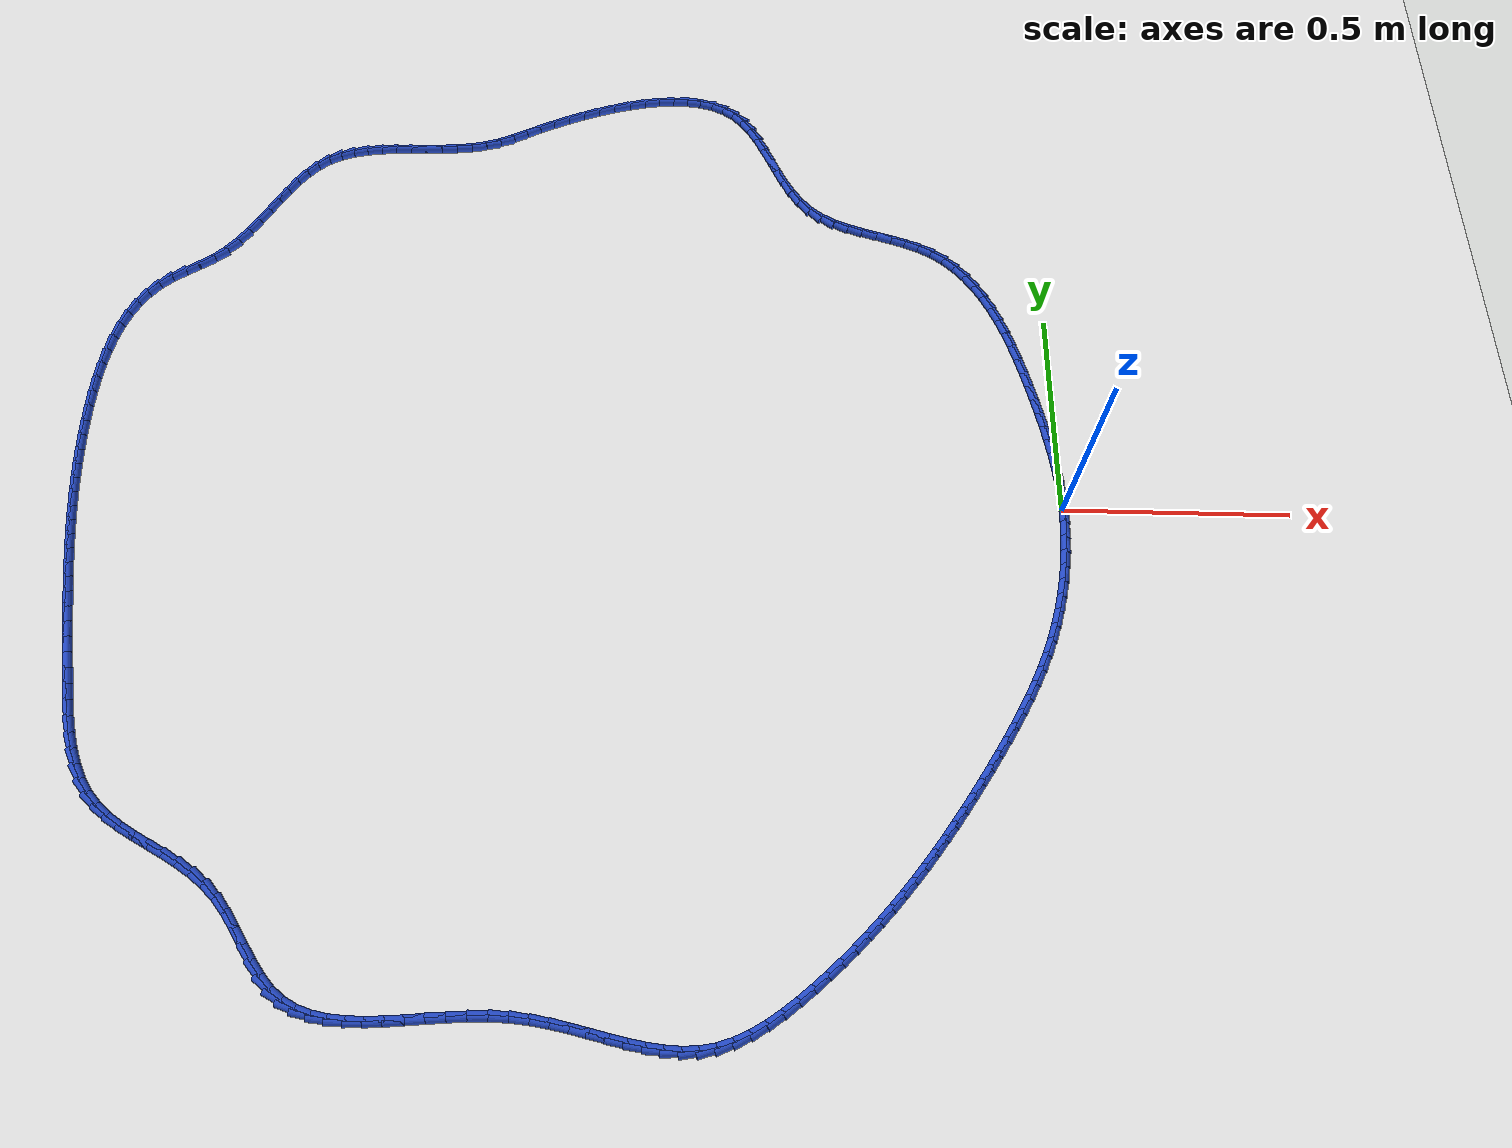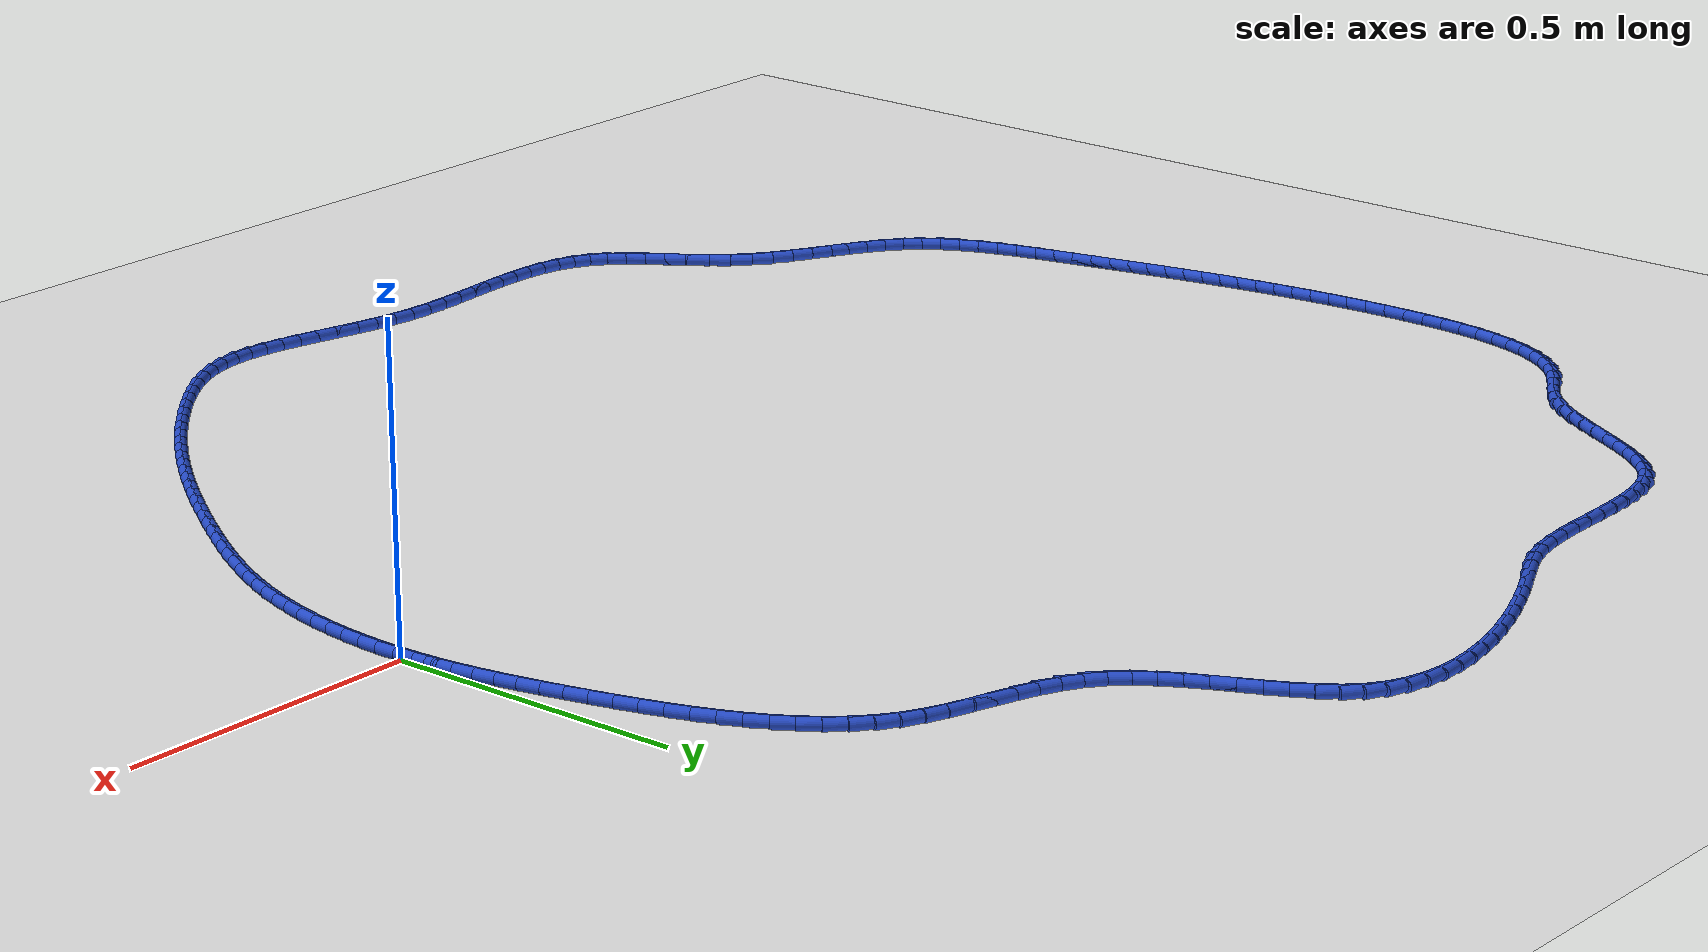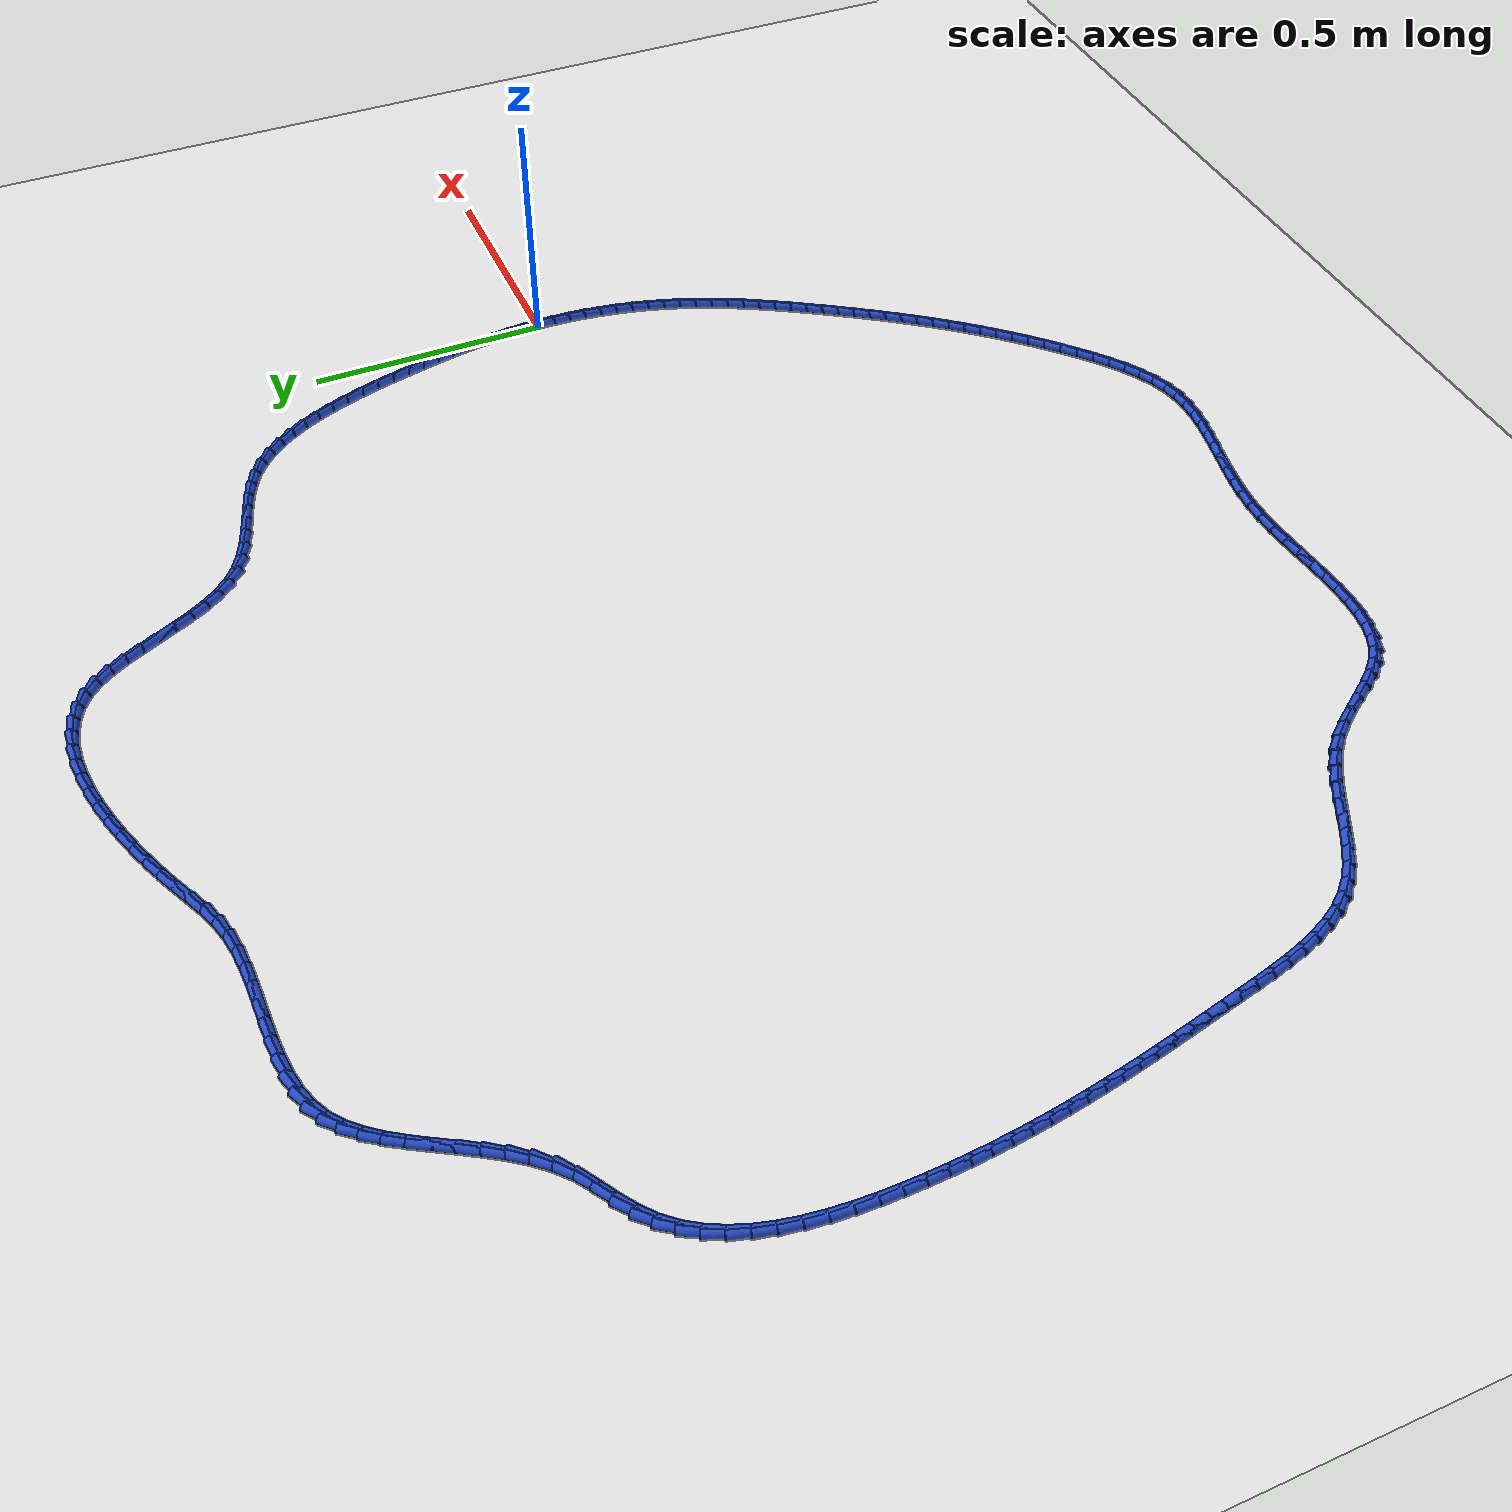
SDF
<sdf version="1.6">
 <world name="default">
  <light name="sun" type="directional">
   <pose>0 0 10 0 -0 0</pose>
   <diffuse>0.8 0.8 0.8 1</diffuse>
   <specular>0.2 0.2 0.2 1</specular>
   <attenuation>
    <range>1000</range>
    <constant>0.9</constant>
    <linear>0.01</linear>
    <quadratic>0.001</quadratic>
   </attenuation>
   <direction>-0.5 0.1 -0.9</direction>
  </light>
  <model name="ground_plane">
   <static>1</static>
   <link name="link">
    <collision name="collision">
     <geometry><plane><normal>0 0 1</normal><size>100 100</size></plane></geometry>
     <surface><friction><ode><mu>100</mu><mu2>50</mu2></ode></friction></surface>
    </collision>
    <visual name="visual">
     <cast_shadows>0</cast_shadows>
     <geometry><plane><normal>0 0 1</normal><size>100 100</size></plane></geometry>
     <material>
      <script><uri>file://media/materials/scripts/gazebo.material</uri><name>Gazebo/WhiteGlow</name></script>
     </material>
    </visual>
   </link>
  </model>
  <gravity>0 0 -9.8</gravity>
  <magnetic_field>6e-06 2.3e-05 -4.2e-05</magnetic_field>
  <atmosphere type="adiabatic"/>
  <physics name="default_physics" default="0" type="ode">
   <max_step_size>0.001</max_step_size>
   <real_time_factor>1</real_time_factor>
   <real_time_update_rate>1000</real_time_update_rate>
  </physics>
  <scene><ambient>0.4 0.4 0.4 1</ambient><background>0.7 0.7 0.7 1</background><shadows>1</shadows></scene>
  <spherical_coordinates>
   <surface_model>EARTH_WGS84</surface_model>
   <latitude_deg>0</latitude_deg>
   <longitude_deg>0</longitude_deg>
   <elevation>0</elevation>
   <heading_deg>0</heading_deg>
  </spherical_coordinates>
  <model name="line">
   <link name="link_0">
    <pose>-3.469446951953614e-17 7.632783294297951e-17 0.01 0 1.57 -1.5332904688426268</pose>
    <collision name="collision">
     <geometry><cylinder><radius>0.01</radius><length>0.08</length></cylinder></geometry>
    </collision>
    <visual name="visual">
     <material>
      <script><name>Gazebo/Blue</name><uri>file://media/materials/scripts/gazebo.material</uri></script>
     </material>
     <geometry><cylinder><radius>0.01</radius><length>0.08</length></cylinder></geometry>
    </visual>
   </link>
   <link name="link_1">
    <pose>-0.0013126352943905112 0.034981728675266506 0.01 0 1.57 -1.4955436835216058</pose>
    <collision name="collision">
     <geometry><cylinder><radius>0.01</radius><length>0.08</length></cylinder></geometry>
    </collision>
    <visual name="visual">
     <material>
      <script><name>Gazebo/Blue</name><uri>file://media/materials/scripts/gazebo.material</uri></script>
     </material>
     <geometry><cylinder><radius>0.01</radius><length>0.08</length></cylinder></geometry>
    </visual>
   </link>
   <link name="link_2">
    <pose>-0.0039356135919354366 0.06977153856625622 0.01 0 1.57 -1.4607083003388548</pose>
    <collision name="collision">
     <geometry><cylinder><radius>0.01</radius><length>0.08</length></cylinder></geometry>
    </collision>
    <visual name="visual">
     <material>
      <script><name>Gazebo/Blue</name><uri>file://media/materials/scripts/gazebo.material</uri></script>
     </material>
     <geometry><cylinder><radius>0.01</radius><length>0.08</length></cylinder></geometry>
    </visual>
   </link>
   <link name="link_3">
    <pose>-0.0077704655635502376 0.10446511571541536 0.01 0 1.57 -1.429122179175878</pose>
    <collision name="collision">
     <geometry><cylinder><radius>0.01</radius><length>0.08</length></cylinder></geometry>
    </collision>
    <visual name="visual">
     <material>
      <script><name>Gazebo/Blue</name><uri>file://media/materials/scripts/gazebo.material</uri></script>
     </material>
     <geometry><cylinder><radius>0.01</radius><length>0.08</length></cylinder></geometry>
    </visual>
   </link>
   <link name="link_4">
    <pose>-0.012718721880150361 0.1391581461651901 0.01 0 1.57 -1.4010318733163856</pose>
    <collision name="collision">
     <geometry><cylinder><radius>0.01</radius><length>0.08</length></cylinder></geometry>
    </collision>
    <visual name="visual">
     <material>
      <script><name>Gazebo/Blue</name><uri>file://media/materials/scripts/gazebo.material</uri></script>
     </material>
     <geometry><cylinder><radius>0.01</radius><length>0.08</length></cylinder></geometry>
    </visual>
   </link>
   <link name="link_5">
    <pose>-0.01868191321265123 0.17394631595802645 0.01 0 1.57 -1.3765954267108529</pose>
    <collision name="collision">
     <geometry><cylinder><radius>0.01</radius><length>0.08</length></cylinder></geometry>
    </collision>
    <visual name="visual">
     <material>
      <script><name>Gazebo/Blue</name><uri>file://media/materials/scripts/gazebo.material</uri></script>
     </material>
     <geometry><cylinder><radius>0.01</radius><length>0.08</length></cylinder></geometry>
    </visual>
   </link>
   <link name="link_6">
    <pose>-0.025561570231968294 0.20892531113637067 0.01 0 1.57 -1.3558899525926105</pose>
    <collision name="collision">
     <geometry><cylinder><radius>0.01</radius><length>0.08</length></cylinder></geometry>
    </collision>
    <visual name="visual">
     <material>
      <script><name>Gazebo/Blue</name><uri>file://media/materials/scripts/gazebo.material</uri></script>
     </material>
     <geometry><cylinder><radius>0.01</radius><length>0.08</length></cylinder></geometry>
    </visual>
   </link>
   <link name="link_7">
    <pose>-0.033259223609016994 0.24419081774266885 0.01 0 1.57 -1.3389220635359205</pose>
    <collision name="collision">
     <geometry><cylinder><radius>0.01</radius><length>0.08</length></cylinder></geometry>
    </collision>
    <visual name="visual">
     <material>
      <script><name>Gazebo/Blue</name><uri>file://media/materials/scripts/gazebo.material</uri></script>
     </material>
     <geometry><cylinder><radius>0.01</radius><length>0.08</length></cylinder></geometry>
    </visual>
   </link>
   <link name="link_8">
    <pose>-0.041676404014712745 0.2798385218193671 0.01 0 1.57 -1.3256276389955242</pose>
    <collision name="collision">
     <geometry><cylinder><radius>0.01</radius><length>0.08</length></cylinder></geometry>
    </collision>
    <visual name="visual">
     <material>
      <script><name>Gazebo/Blue</name><uri>file://media/materials/scripts/gazebo.material</uri></script>
     </material>
     <geometry><cylinder><radius>0.01</radius><length>0.08</length></cylinder></geometry>
    </visual>
   </link>
   <link name="link_9">
    <pose>-0.05071496901925 0.315963605657907 0.01 0 1.57 -1.313118206622053</pose>
    <collision name="collision">
     <geometry><cylinder><radius>0.01</radius><length>0.08</length></cylinder></geometry>
    </collision>
    <visual name="visual">
     <material>
      <script><name>Gazebo/Blue</name><uri>file://media/materials/scripts/gazebo.material</uri></script>
     </material>
     <geometry><cylinder><radius>0.01</radius><length>0.08</length></cylinder></geometry>
    </visual>
   </link>
   <link name="link_10">
    <pose>-0.060354562354739294 0.35254138326086565 0.01 0 1.57 -1.2949289522902876</pose>
    <collision name="collision">
     <geometry><cylinder><radius>0.01</radius><length>0.08</length></cylinder></geometry>
    </collision>
    <visual name="visual">
     <material>
      <script><name>Gazebo/Blue</name><uri>file://media/materials/scripts/gazebo.material</uri></script>
     </material>
     <geometry><cylinder><radius>0.01</radius><length>0.08</length></cylinder></geometry>
    </visual>
   </link>
   <link name="link_11">
    <pose>-0.07075274260871864 0.38927300226551403 0.01 0 1.57 -1.2699642282858752</pose>
    <collision name="collision">
     <geometry><cylinder><radius>0.01</radius><length>0.08</length></cylinder></geometry>
    </collision>
    <visual name="visual">
     <material>
      <script><name>Gazebo/Blue</name><uri>file://media/materials/scripts/gazebo.material</uri></script>
     </material>
     <geometry><cylinder><radius>0.01</radius><length>0.08</length></cylinder></geometry>
    </visual>
   </link>
   <link name="link_12">
    <pose>-0.08209183255353676 0.4258214487597515 0.01 0 1.57 -1.2377750774524687</pose>
    <collision name="collision">
     <geometry><cylinder><radius>0.01</radius><length>0.08</length></cylinder></geometry>
    </collision>
    <visual name="visual">
     <material>
      <script><name>Gazebo/Blue</name><uri>file://media/materials/scripts/gazebo.material</uri></script>
     </material>
     <geometry><cylinder><radius>0.01</radius><length>0.08</length></cylinder></geometry>
    </visual>
   </link>
   <link name="link_13">
    <pose>-0.09455415496154239 0.4618497088314772 0.01 0 1.57 -1.197678199481396</pose>
    <collision name="collision">
     <geometry><cylinder><radius>0.01</radius><length>0.08</length></cylinder></geometry>
    </collision>
    <visual name="visual">
     <material>
      <script><name>Gazebo/Blue</name><uri>file://media/materials/scripts/gazebo.material</uri></script>
     </material>
     <geometry><cylinder><radius>0.01</radius><length>0.08</length></cylinder></geometry>
    </visual>
   </link>
   <link name="link_14">
    <pose>-0.1083220326050843 0.4970207685685908 0.01 0 1.57 -1.148770588921844</pose>
    <collision name="collision">
     <geometry><cylinder><radius>0.01</radius><length>0.08</length></cylinder></geometry>
    </collision>
    <visual name="visual">
     <material>
      <script><name>Gazebo/Blue</name><uri>file://media/materials/scripts/gazebo.material</uri></script>
     </material>
     <geometry><cylinder><radius>0.01</radius><length>0.08</length></cylinder></geometry>
    </visual>
   </link>
   <link name="link_15">
    <pose>-0.12357778825651114 0.5309976140589914 0.01 0 1.57 -1.0899621455450785</pose>
    <collision name="collision">
     <geometry><cylinder><radius>0.01</radius><length>0.08</length></cylinder></geometry>
    </collision>
    <visual name="visual">
     <material>
      <script><name>Gazebo/Blue</name><uri>file://media/materials/scripts/gazebo.material</uri></script>
     </material>
     <geometry><cylinder><radius>0.01</radius><length>0.08</length></cylinder></geometry>
    </visual>
   </link>
   <link name="link_16">
    <pose>-0.14050374468817176 0.5634432313905783 0.01 0 1.57 -1.0200519366504543</pose>
    <collision name="collision">
     <geometry><cylinder><radius>0.01</radius><length>0.08</length></cylinder></geometry>
    </collision>
    <visual name="visual">
     <material>
      <script><name>Gazebo/Blue</name><uri>file://media/materials/scripts/gazebo.material</uri></script>
     </material>
     <geometry><cylinder><radius>0.01</radius><length>0.08</length></cylinder></geometry>
    </visual>
   </link>
   <link name="link_17">
    <pose>-0.15928222467241485 0.594020606651251 0.01 0 1.57 -0.9378846530435814</pose>
    <collision name="collision">
     <geometry><cylinder><radius>0.01</radius><length>0.08</length></cylinder></geometry>
    </collision>
    <visual name="visual">
     <material>
      <script><name>Gazebo/Blue</name><uri>file://media/materials/scripts/gazebo.material</uri></script>
     </material>
     <geometry><cylinder><radius>0.01</radius><length>0.08</length></cylinder></geometry>
    </visual>
   </link>
   <link name="link_18">
    <pose>-0.18009555098158903 0.6223927259289086 0.01 0 1.57 -0.8426285628527114</pose>
    <collision name="collision">
     <geometry><cylinder><radius>0.01</radius><length>0.08</length></cylinder></geometry>
    </collision>
    <visual name="visual">
     <material>
      <script><name>Gazebo/Blue</name><uri>file://media/materials/scripts/gazebo.material</uri></script>
     </material>
     <geometry><cylinder><radius>0.01</radius><length>0.08</length></cylinder></geometry>
    </visual>
   </link>
   <link name="link_19">
    <pose>-0.2031260463880432 0.6482225753114509 0.01 0 1.57 -0.7341946461471444</pose>
    <collision name="collision">
     <geometry><cylinder><radius>0.01</radius><length>0.08</length></cylinder></geometry>
    </collision>
    <visual name="visual">
     <material>
      <script><name>Gazebo/Blue</name><uri>file://media/materials/scripts/gazebo.material</uri></script>
     </material>
     <geometry><cylinder><radius>0.01</radius><length>0.08</length></cylinder></geometry>
    </visual>
   </link>
   <link name="link_20">
    <pose>-0.22855603366412608 0.6711731408867769 0.01 0 1.57 -0.6137386064435449</pose>
    <collision name="collision">
     <geometry><cylinder><radius>0.01</radius><length>0.08</length></cylinder></geometry>
    </collision>
    <visual name="visual">
     <material>
      <script><name>Gazebo/Blue</name><uri>file://media/materials/scripts/gazebo.material</uri></script>
     </material>
     <geometry><cylinder><radius>0.01</radius><length>0.08</length></cylinder></geometry>
    </visual>
   </link>
   <link name="link_21">
    <pose>-0.25656783558218627 0.6909074087427858 0.01 0 1.57 -0.4868756990810768</pose>
    <collision name="collision">
     <geometry><cylinder><radius>0.01</radius><length>0.08</length></cylinder></geometry>
    </collision>
    <visual name="visual">
     <material>
      <script><name>Gazebo/Blue</name><uri>file://media/materials/scripts/gazebo.material</uri></script>
     </material>
     <geometry><cylinder><radius>0.01</radius><length>0.08</length></cylinder></geometry>
    </visual>
   </link>
   <link name="link_22">
    <pose>-0.28728621489683515 0.7071691546602961 0.01 0 1.57 -0.3842373551132896</pose>
    <collision name="collision">
     <geometry><cylinder><radius>0.01</radius><length>0.08</length></cylinder></geometry>
    </collision>
    <visual name="visual">
     <material>
      <script><name>Gazebo/Blue</name><uri>file://media/materials/scripts/gazebo.material</uri></script>
     </material>
     <geometry><cylinder><radius>0.01</radius><length>0.08</length></cylinder></geometry>
    </visual>
   </link>
   <link name="link_23">
    <pose>-0.3202649390582101 0.7205035880735475 0.01 0 1.57 -0.3197110012479004</pose>
    <collision name="collision">
     <geometry><cylinder><radius>0.01</radius><length>0.08</length></cylinder></geometry>
    </collision>
    <visual name="visual">
     <material>
      <script><name>Gazebo/Blue</name><uri>file://media/materials/scripts/gazebo.material</uri></script>
     </material>
     <geometry><cylinder><radius>0.01</radius><length>0.08</length></cylinder></geometry>
    </visual>
   </link>
   <link name="link_24">
    <pose>-0.3547312015933717 0.7319142887925671 0.01 0 1.57 -0.28996406516827006</pose>
    <collision name="collision">
     <geometry><cylinder><radius>0.01</radius><length>0.08</length></cylinder></geometry>
    </collision>
    <visual name="visual">
     <material>
      <script><name>Gazebo/Blue</name><uri>file://media/materials/scripts/gazebo.material</uri></script>
     </material>
     <geometry><cylinder><radius>0.01</radius><length>0.08</length></cylinder></geometry>
    </visual>
   </link>
   <link name="link_25">
    <pose>-0.3899083569190071 0.7424102250994551 0.01 0 1.57 -0.29293816506218145</pose>
    <collision name="collision">
     <geometry><cylinder><radius>0.01</radius><length>0.08</length></cylinder></geometry>
    </collision>
    <visual name="visual">
     <material>
      <script><name>Gazebo/Blue</name><uri>file://media/materials/scripts/gazebo.material</uri></script>
     </material>
     <geometry><cylinder><radius>0.01</radius><length>0.08</length></cylinder></geometry>
    </visual>
   </link>
   <link name="link_26">
    <pose>-0.42501975945180376 0.7530003652763122 0.01 0 1.57 -0.3288327986890378</pose>
    <collision name="collision">
     <geometry><cylinder><radius>0.01</radius><length>0.08</length></cylinder></geometry>
    </collision>
    <visual name="visual">
     <material>
      <script><name>Gazebo/Blue</name><uri>file://media/materials/scripts/gazebo.material</uri></script>
     </material>
     <geometry><cylinder><radius>0.01</radius><length>0.08</length></cylinder></geometry>
    </visual>
   </link>
   <link name="link_27">
    <pose>-0.4592887636084485 0.764693677605239 0.01 0 1.57 -0.4000330242904313</pose>
    <collision name="collision">
     <geometry><cylinder><radius>0.01</radius><length>0.08</length></cylinder></geometry>
    </collision>
    <visual name="visual">
     <material>
      <script><name>Gazebo/Blue</name><uri>file://media/materials/scripts/gazebo.material</uri></script>
     </material>
     <geometry><cylinder><radius>0.01</radius><length>0.08</length></cylinder></geometry>
    </visual>
   </link>
   <link name="link_28">
    <pose>-0.4919387238056287 0.7784991303683356 0.01 0 1.57 -0.5100899118179136</pose>
    <collision name="collision">
     <geometry><cylinder><radius>0.01</radius><length>0.08</length></cylinder></geometry>
    </collision>
    <visual name="visual">
     <material>
      <script><name>Gazebo/Blue</name><uri>file://media/materials/scripts/gazebo.material</uri></script>
     </material>
     <geometry><cylinder><radius>0.01</radius><length>0.08</length></cylinder></geometry>
    </visual>
   </link>
   <link name="link_29">
    <pose>-0.5221929944600313 0.795425691847703 0.01 0 1.57 -0.6606575660997491</pose>
    <collision name="collision">
     <geometry><cylinder><radius>0.01</radius><length>0.08</length></cylinder></geometry>
    </collision>
    <visual name="visual">
     <material>
      <script><name>Gazebo/Blue</name><uri>file://media/materials/scripts/gazebo.material</uri></script>
     </material>
     <geometry><cylinder><radius>0.01</radius><length>0.08</length></cylinder></geometry>
    </visual>
   </link>
   <link name="link_30">
    <pose>-0.5492794596210904 0.8164761845905089 0.01 0 1.57 -0.8241629922289854</pose>
    <collision name="collision">
     <geometry><cylinder><radius>0.01</radius><length>0.08</length></cylinder></geometry>
    </collision>
    <visual name="visual">
     <material>
      <script><name>Gazebo/Blue</name><uri>file://media/materials/scripts/gazebo.material</uri></script>
     </material>
     <geometry><cylinder><radius>0.01</radius><length>0.08</length></cylinder></geometry>
    </visual>
   </link>
   <link name="link_31">
    <pose>-0.5729030590916553 0.8420061693519507 0.01 0 1.57 -0.9521379869353082</pose>
    <collision name="collision">
     <geometry><cylinder><radius>0.01</radius><length>0.08</length></cylinder></geometry>
    </collision>
    <visual name="visual">
     <material>
      <script><name>Gazebo/Blue</name><uri>file://media/materials/scripts/gazebo.material</uri></script>
     </material>
     <geometry><cylinder><radius>0.01</radius><length>0.08</length></cylinder></geometry>
    </visual>
   </link>
   <link name="link_32">
    <pose>-0.5936593059784434 0.8711628909442432 0.01 0 1.57 -1.0419528258431332</pose>
    <collision name="collision">
     <geometry><cylinder><radius>0.01</radius><length>0.08</length></cylinder></geometry>
    </collision>
    <visual name="visual">
     <material>
      <script><name>Gazebo/Blue</name><uri>file://media/materials/scripts/gazebo.material</uri></script>
     </material>
     <geometry><cylinder><radius>0.01</radius><length>0.08</length></cylinder></geometry>
    </visual>
   </link>
   <link name="link_33">
    <pose>-0.6122411909532381 0.9029613381424624 0.01 0 1.57 -1.0982707406018197</pose>
    <collision name="collision">
     <geometry><cylinder><radius>0.01</radius><length>0.08</length></cylinder></geometry>
    </collision>
    <visual name="visual">
     <material>
      <script><name>Gazebo/Blue</name><uri>file://media/materials/scripts/gazebo.material</uri></script>
     </material>
     <geometry><cylinder><radius>0.01</radius><length>0.08</length></cylinder></geometry>
    </visual>
   </link>
   <link name="link_34">
    <pose>-0.6293417046878228 0.9364164997216838 0.01 0 1.57 -1.1249152284754242</pose>
    <collision name="collision">
     <geometry><cylinder><radius>0.01</radius><length>0.08</length></cylinder></geometry>
    </collision>
    <visual name="visual">
     <material>
      <script><name>Gazebo/Blue</name><uri>file://media/materials/scripts/gazebo.material</uri></script>
     </material>
     <geometry><cylinder><radius>0.01</radius><length>0.08</length></cylinder></geometry>
    </visual>
   </link>
   <link name="link_35">
    <pose>-0.6456538378539805 0.9705433644569835 0.01 0 1.57 -1.1236072344784087</pose>
    <collision name="collision">
     <geometry><cylinder><radius>0.01</radius><length>0.08</length></cylinder></geometry>
    </collision>
    <visual name="visual">
     <material>
      <script><name>Gazebo/Blue</name><uri>file://media/materials/scripts/gazebo.material</uri></script>
     </material>
     <geometry><cylinder><radius>0.01</radius><length>0.08</length></cylinder></geometry>
    </visual>
   </link>
   <link name="link_36">
    <pose>-0.6618705811234942 1.0043569211234369 0.01 0 1.57 -1.093545144004028</pose>
    <collision name="collision">
     <geometry><cylinder><radius>0.01</radius><length>0.08</length></cylinder></geometry>
    </collision>
    <visual name="visual">
     <material>
      <script><name>Gazebo/Blue</name><uri>file://media/materials/scripts/gazebo.material</uri></script>
     </material>
     <geometry><cylinder><radius>0.01</radius><length>0.08</length></cylinder></geometry>
    </visual>
   </link>
   <link name="link_37">
    <pose>-0.6786849251681473 1.03687215849612 0.01 0 1.57 -1.0312092568120015</pose>
    <collision name="collision">
     <geometry><cylinder><radius>0.01</radius><length>0.08</length></cylinder></geometry>
    </collision>
    <visual name="visual">
     <material>
      <script><name>Gazebo/Blue</name><uri>file://media/materials/scripts/gazebo.material</uri></script>
     </material>
     <geometry><cylinder><radius>0.01</radius><length>0.08</length></cylinder></geometry>
    </visual>
   </link>
   <link name="link_38">
    <pose>-0.6967898606597228 1.067104065350108 0.01 0 1.57 -0.9304871265405741</pose>
    <collision name="collision">
     <geometry><cylinder><radius>0.01</radius><length>0.08</length></cylinder></geometry>
    </collision>
    <visual name="visual">
     <material>
      <script><name>Gazebo/Blue</name><uri>file://media/materials/scripts/gazebo.material</uri></script>
     </material>
     <geometry><cylinder><radius>0.01</radius><length>0.08</length></cylinder></geometry>
    </visual>
   </link>
   <link name="link_39">
    <pose>-0.7168783782700046 1.0940676304604777 0.01 0 1.57 -0.784192610109702</pose>
    <collision name="collision">
     <geometry><cylinder><radius>0.01</radius><length>0.08</length></cylinder></geometry>
    </collision>
    <visual name="visual">
     <material>
      <script><name>Gazebo/Blue</name><uri>file://media/materials/scripts/gazebo.material</uri></script>
     </material>
     <geometry><cylinder><radius>0.01</radius><length>0.08</length></cylinder></geometry>
    </visual>
   </link>
   <link name="link_40">
    <pose>-0.739643444233237 1.116777873488885 0.01 0 1.57 -0.5998632557916628</pose>
    <collision name="collision">
     <geometry><cylinder><radius>0.01</radius><length>0.08</length></cylinder></geometry>
    </collision>
    <visual name="visual">
     <material>
      <script><name>Gazebo/Blue</name><uri>file://media/materials/scripts/gazebo.material</uri></script>
     </material>
     <geometry><cylinder><radius>0.01</radius><length>0.08</length></cylinder></geometry>
    </visual>
   </link>
   <link name="link_41">
    <pose>-0.7655714149027426 1.134510948129543 0.01 0 1.57 -0.42101132649204476</pose>
    <collision name="collision">
     <geometry><cylinder><radius>0.01</radius><length>0.08</length></cylinder></geometry>
    </collision>
    <visual name="visual">
     <material>
      <script><name>Gazebo/Blue</name><uri>file://media/materials/scripts/gazebo.material</uri></script>
     </material>
     <geometry><cylinder><radius>0.01</radius><length>0.08</length></cylinder></geometry>
    </visual>
   </link>
   <link name="link_42">
    <pose>-0.7944404477542465 1.147438099966423 0.01 0 1.57 -0.2635994863551069</pose>
    <collision name="collision">
     <geometry><cylinder><radius>0.01</radius><length>0.08</length></cylinder></geometry>
    </collision>
    <visual name="visual">
     <material>
      <script><name>Gazebo/Blue</name><uri>file://media/materials/scripts/gazebo.material</uri></script>
     </material>
     <geometry><cylinder><radius>0.01</radius><length>0.08</length></cylinder></geometry>
    </visual>
   </link>
   <link name="link_43">
    <pose>-0.825877083795018 1.1559222024941886 0.01 0 1.57 -0.1302084017572697</pose>
    <collision name="collision">
     <geometry><cylinder><radius>0.01</radius><length>0.08</length></cylinder></geometry>
    </collision>
    <visual name="visual">
     <material>
      <script><name>Gazebo/Blue</name><uri>file://media/materials/scripts/gazebo.material</uri></script>
     </material>
     <geometry><cylinder><radius>0.01</radius><length>0.08</length></cylinder></geometry>
    </visual>
   </link>
   <link name="link_44">
    <pose>-0.8595078640323267 1.1603261292075036 0.01 0 1.57 -0.01936559035907604</pose>
    <collision name="collision">
     <geometry><cylinder><radius>0.01</radius><length>0.08</length></cylinder></geometry>
    </collision>
    <visual name="visual">
     <material>
      <script><name>Gazebo/Blue</name><uri>file://media/materials/scripts/gazebo.material</uri></script>
     </material>
     <geometry><cylinder><radius>0.01</radius><length>0.08</length></cylinder></geometry>
    </visual>
   </link>
   <link name="link_45">
    <pose>-0.8949593294734419 1.1610127536010317 0.01 0 1.57 0.07217519848140119</pose>
    <collision name="collision">
     <geometry><cylinder><radius>0.01</radius><length>0.08</length></cylinder></geometry>
    </collision>
    <visual name="visual">
     <material>
      <script><name>Gazebo/Blue</name><uri>file://media/materials/scripts/gazebo.material</uri></script>
     </material>
     <geometry><cylinder><radius>0.01</radius><length>0.08</length></cylinder></geometry>
    </visual>
   </link>
   <link name="link_46">
    <pose>-0.9318580211256334 1.158344949169437 0.01 0 1.57 0.14794951030648643</pose>
    <collision name="collision">
     <geometry><cylinder><radius>0.01</radius><length>0.08</length></cylinder></geometry>
    </collision>
    <visual name="visual">
     <material>
      <script><name>Gazebo/Blue</name><uri>file://media/materials/scripts/gazebo.material</uri></script>
     </material>
     <geometry><cylinder><radius>0.01</radius><length>0.08</length></cylinder></geometry>
    </visual>
   </link>
   <link name="link_47">
    <pose>-0.9698304799961703 1.1526855894073833 0.01 0 1.57 0.21111855221193981</pose>
    <collision name="collision">
     <geometry><cylinder><radius>0.01</radius><length>0.08</length></cylinder></geometry>
    </collision>
    <visual name="visual">
     <material>
      <script><name>Gazebo/Blue</name><uri>file://media/materials/scripts/gazebo.material</uri></script>
     </material>
     <geometry><cylinder><radius>0.01</radius><length>0.08</length></cylinder></geometry>
    </visual>
   </link>
   <link name="link_48">
    <pose>-1.008503247092322 1.144397547809534 0.01 0 1.57 0.26428421225724313</pose>
    <collision name="collision">
     <geometry><cylinder><radius>0.01</radius><length>0.08</length></cylinder></geometry>
    </collision>
    <visual name="visual">
     <material>
      <script><name>Gazebo/Blue</name><uri>file://media/materials/scripts/gazebo.material</uri></script>
     </material>
     <geometry><cylinder><radius>0.01</radius><length>0.08</length></cylinder></geometry>
    </visual>
   </link>
   <link name="link_49">
    <pose>-1.0475028634213581 1.1338436978705528 0.01 0 1.57 0.3095125050177478</pose>
    <collision name="collision">
     <geometry><cylinder><radius>0.01</radius><length>0.08</length></cylinder></geometry>
    </collision>
    <visual name="visual">
     <material>
      <script><name>Gazebo/Blue</name><uri>file://media/materials/scripts/gazebo.material</uri></script>
     </material>
     <geometry><cylinder><radius>0.01</radius><length>0.08</length></cylinder></geometry>
    </visual>
   </link>
   <link name="link_50">
    <pose>-1.0864558699905482 1.1213869130851035 0.01 0 1.57 0.34842413715925036</pose>
    <collision name="collision">
     <geometry><cylinder><radius>0.01</radius><length>0.08</length></cylinder></geometry>
    </collision>
    <visual name="visual">
     <material>
      <script><name>Gazebo/Blue</name><uri>file://media/materials/scripts/gazebo.material</uri></script>
     </material>
     <geometry><cylinder><radius>0.01</radius><length>0.08</length></cylinder></geometry>
    </visual>
   </link>
   <link name="link_51">
    <pose>-1.124988807807162 1.1073900669478505 0.01 0 1.57 0.3822929926549289</pose>
    <collision name="collision">
     <geometry><cylinder><radius>0.01</radius><length>0.08</length></cylinder></geometry>
    </collision>
    <visual name="visual">
     <material>
      <script><name>Gazebo/Blue</name><uri>file://media/materials/scripts/gazebo.material</uri></script>
     </material>
     <geometry><cylinder><radius>0.01</radius><length>0.08</length></cylinder></geometry>
    </visual>
   </link>
   <link name="link_52">
    <pose>-1.1627282178784681 1.0922160329534571 0.01 0 1.57 0.4121330123331484</pose>
    <collision name="collision">
     <geometry><cylinder><radius>0.01</radius><length>0.08</length></cylinder></geometry>
    </collision>
    <visual name="visual">
     <material>
      <script><name>Gazebo/Blue</name><uri>file://media/materials/scripts/gazebo.material</uri></script>
     </material>
     <geometry><cylinder><radius>0.01</radius><length>0.08</length></cylinder></geometry>
    </visual>
   </link>
   <link name="link_53">
    <pose>-1.1993006412117366 1.076227684596587 0.01 0 1.57 0.4387705920176841</pose>
    <collision name="collision">
     <geometry><cylinder><radius>0.01</radius><length>0.08</length></cylinder></geometry>
    </collision>
    <visual name="visual">
     <material>
      <script><name>Gazebo/Blue</name><uri>file://media/materials/scripts/gazebo.material</uri></script>
     </material>
     <geometry><cylinder><radius>0.01</radius><length>0.08</length></cylinder></geometry>
    </visual>
   </link>
   <link name="link_54">
    <pose>-1.234332618814237 1.0597878953719038 0.01 0 1.57 0.46091643209618305</pose>
    <collision name="collision">
     <geometry><cylinder><radius>0.01</radius><length>0.08</length></cylinder></geometry>
    </collision>
    <visual name="visual">
     <material>
      <script><name>Gazebo/Blue</name><uri>file://media/materials/scripts/gazebo.material</uri></script>
     </material>
     <geometry><cylinder><radius>0.01</radius><length>0.08</length></cylinder></geometry>
    </visual>
   </link>
   <link name="link_55">
    <pose>-1.2675317954856624 1.0433014937818326 0.01 0 1.57 0.45388255259020177</pose>
    <collision name="collision">
     <geometry><cylinder><radius>0.01</radius><length>0.08</length></cylinder></geometry>
    </collision>
    <visual name="visual">
     <material>
      <script><name>Gazebo/Blue</name><uri>file://media/materials/scripts/gazebo.material</uri></script>
     </material>
     <geometry><cylinder><radius>0.01</radius><length>0.08</length></cylinder></geometry>
    </visual>
   </link>
   <link name="link_56">
    <pose>-1.2995694940208837 1.0276718191451042 0.01 0 1.57 0.3983536954741635</pose>
    <collision name="collision">
     <geometry><cylinder><radius>0.01</radius><length>0.08</length></cylinder></geometry>
    </collision>
    <visual name="visual">
     <material>
      <script><name>Gazebo/Blue</name><uri>file://media/materials/scripts/gazebo.material</uri></script>
     </material>
     <geometry><cylinder><radius>0.01</radius><length>0.08</length></cylinder></geometry>
    </visual>
   </link>
   <link name="link_57">
    <pose>-1.3317488089567595 1.0141290264267466 0.01 0 1.57 0.29727718201862086</pose>
    <collision name="collision">
     <geometry><cylinder><radius>0.01</radius><length>0.08</length></cylinder></geometry>
    </collision>
    <visual name="visual">
     <material>
      <script><name>Gazebo/Blue</name><uri>file://media/materials/scripts/gazebo.material</uri></script>
     </material>
     <geometry><cylinder><radius>0.01</radius><length>0.08</length></cylinder></geometry>
    </visual>
   </link>
   <link name="link_58">
    <pose>-1.3653255453676352 1.0038426122003508 0.01 0 1.57 0.1935938666769805</pose>
    <collision name="collision">
     <geometry><cylinder><radius>0.01</radius><length>0.08</length></cylinder></geometry>
    </collision>
    <visual name="visual">
     <material>
      <script><name>Gazebo/Blue</name><uri>file://media/materials/scripts/gazebo.material</uri></script>
     </material>
     <geometry><cylinder><radius>0.01</radius><length>0.08</length></cylinder></geometry>
    </visual>
   </link>
   <link name="link_59">
    <pose>-1.4006245270764717 0.9969222742285392 0.01 0 1.57 0.11685259480461863</pose>
    <collision name="collision">
     <geometry><cylinder><radius>0.01</radius><length>0.08</length></cylinder></geometry>
    </collision>
    <visual name="visual">
     <material>
      <script><name>Gazebo/Blue</name><uri>file://media/materials/scripts/gazebo.material</uri></script>
     </material>
     <geometry><cylinder><radius>0.01</radius><length>0.08</length></cylinder></geometry>
    </visual>
   </link>
   <link name="link_60">
    <pose>-1.4372225093121849 0.9926261332896386 0.01 0 1.57 0.06500117083351974</pose>
    <collision name="collision">
     <geometry><cylinder><radius>0.01</radius><length>0.08</length></cylinder></geometry>
    </collision>
    <visual name="visual">
     <material>
      <script><name>Gazebo/Blue</name><uri>file://media/materials/scripts/gazebo.material</uri></script>
     </material>
     <geometry><cylinder><radius>0.01</radius><length>0.08</length></cylinder></geometry>
    </visual>
   </link>
   <link name="link_61">
    <pose>-1.4746750998531593 0.9901882365913276 0.01 0 1.57 0.035524021875939275</pose>
    <collision name="collision">
     <geometry><cylinder><radius>0.01</radius><length>0.08</length></cylinder></geometry>
    </collision>
    <visual name="visual">
     <material>
      <script><name>Gazebo/Blue</name><uri>file://media/materials/scripts/gazebo.material</uri></script>
     </material>
     <geometry><cylinder><radius>0.01</radius><length>0.08</length></cylinder></geometry>
    </visual>
   </link>
   <link name="link_62">
    <pose>-1.5125379064777815 0.9888426313412858 0.01 0 1.57 0.026937798888096137</pose>
    <collision name="collision">
     <geometry><cylinder><radius>0.01</radius><length>0.08</length></cylinder></geometry>
    </collision>
    <visual name="visual">
     <material>
      <script><name>Gazebo/Blue</name><uri>file://media/materials/scripts/gazebo.material</uri></script>
     </material>
     <geometry><cylinder><radius>0.01</radius><length>0.08</length></cylinder></geometry>
    </visual>
   </link>
   <link name="link_63">
    <pose>-1.5503665369644353 0.987823364747191 0.01 0 1.57 0.039039814356765554</pose>
    <collision name="collision">
     <geometry><cylinder><radius>0.01</radius><length>0.08</length></cylinder></geometry>
    </collision>
    <visual name="visual">
     <material>
      <script><name>Gazebo/Blue</name><uri>file://media/materials/scripts/gazebo.material</uri></script>
     </material>
     <geometry><cylinder><radius>0.01</radius><length>0.08</length></cylinder></geometry>
    </visual>
   </link>
   <link name="link_64">
    <pose>-1.5877165990915065 0.9863644840167225 0.01 0 1.57 0.07301462424751472</pose>
    <collision name="collision">
     <geometry><cylinder><radius>0.01</radius><length>0.08</length></cylinder></geometry>
    </collision>
    <visual name="visual">
     <material>
      <script><name>Gazebo/Blue</name><uri>file://media/materials/scripts/gazebo.material</uri></script>
     </material>
     <geometry><cylinder><radius>0.01</radius><length>0.08</length></cylinder></geometry>
    </visual>
   </link>
   <link name="link_65">
    <pose>-1.6241437006373802 0.9837000363575585 0.01 0 1.57 0.13146778592813693</pose>
    <collision name="collision">
     <geometry><cylinder><radius>0.01</radius><length>0.08</length></cylinder></geometry>
    </collision>
    <visual name="visual">
     <material>
      <script><name>Gazebo/Blue</name><uri>file://media/materials/scripts/gazebo.material</uri></script>
     </material>
     <geometry><cylinder><radius>0.01</radius><length>0.08</length></cylinder></geometry>
    </visual>
   </link>
   <link name="link_66">
    <pose>-1.6592034493804422 0.9790640689773785 0.01 0 1.57 0.21823882658381957</pose>
    <collision name="collision">
     <geometry><cylinder><radius>0.01</radius><length>0.08</length></cylinder></geometry>
    </collision>
    <visual name="visual">
     <material>
      <script><name>Gazebo/Blue</name><uri>file://media/materials/scripts/gazebo.material</uri></script>
     </material>
     <geometry><cylinder><radius>0.01</radius><length>0.08</length></cylinder></geometry>
    </visual>
   </link>
   <link name="link_67">
    <pose>-1.692451453099077 0.9716906290838608 0.01 0 1.57 0.3375286405750476</pose>
    <collision name="collision">
     <geometry><cylinder><radius>0.01</radius><length>0.08</length></cylinder></geometry>
    </collision>
    <visual name="visual">
     <material>
      <script><name>Gazebo/Blue</name><uri>file://media/materials/scripts/gazebo.material</uri></script>
     </material>
     <geometry><cylinder><radius>0.01</radius><length>0.08</length></cylinder></geometry>
    </visual>
   </link>
   <link name="link_68">
    <pose>-1.7234433195716696 0.9608137638846841 0.01 0 1.57 0.49153873706173296</pose>
    <collision name="collision">
     <geometry><cylinder><radius>0.01</radius><length>0.08</length></cylinder></geometry>
    </collision>
    <visual name="visual">
     <material>
      <script><name>Gazebo/Blue</name><uri>file://media/materials/scripts/gazebo.material</uri></script>
     </material>
     <geometry><cylinder><radius>0.01</radius><length>0.08</length></cylinder></geometry>
    </visual>
   </link>
   <link name="link_69">
    <pose>-1.7517346639520843 0.945667531974825 0.01 0 1.57 0.665476043277595</pose>
    <collision name="collision">
     <geometry><cylinder><radius>0.01</radius><length>0.08</length></cylinder></geometry>
    </collision>
    <visual name="visual">
     <material>
      <script><name>Gazebo/Blue</name><uri>file://media/materials/scripts/gazebo.material</uri></script>
     </material>
     <geometry><cylinder><radius>0.01</radius><length>0.08</length></cylinder></geometry>
    </visual>
   </link>
   <link name="link_70">
    <pose>-1.7770716135332105 0.9257801313279211 0.01 0 1.57 0.8115602309052364</pose>
    <collision name="collision">
     <geometry><cylinder><radius>0.01</radius><length>0.08</length></cylinder></geometry>
    </collision>
    <visual name="visual">
     <material>
      <script><name>Gazebo/Blue</name><uri>file://media/materials/scripts/gazebo.material</uri></script>
     </material>
     <geometry><cylinder><radius>0.01</radius><length>0.08</length></cylinder></geometry>
    </visual>
   </link>
   <link name="link_71">
    <pose>-1.7998864612433232 0.9017391587290498 0.01 0 1.57 0.9190897820527137</pose>
    <collision name="collision">
     <geometry><cylinder><radius>0.01</radius><length>0.08</length></cylinder></geometry>
    </collision>
    <visual name="visual">
     <material>
      <script><name>Gazebo/Blue</name><uri>file://media/materials/scripts/gazebo.material</uri></script>
     </material>
     <geometry><cylinder><radius>0.01</radius><length>0.08</length></cylinder></geometry>
    </visual>
   </link>
   <link name="link_72">
    <pose>-1.820765926047249 0.87437063555225 0.01 0 1.57 0.9917130987837733</pose>
    <collision name="collision">
     <geometry><cylinder><radius>0.01</radius><length>0.08</length></cylinder></geometry>
    </collision>
    <visual name="visual">
     <material>
      <script><name>Gazebo/Blue</name><uri>file://media/materials/scripts/gazebo.material</uri></script>
     </material>
     <geometry><cylinder><radius>0.01</radius><length>0.08</length></cylinder></geometry>
    </visual>
   </link>
   <link name="link_73">
    <pose>-1.840296726909814 0.8445005831715621 0.01 0 1.57 1.0340790243813807</pose>
    <collision name="collision">
     <geometry><cylinder><radius>0.01</radius><length>0.08</length></cylinder></geometry>
    </collision>
    <visual name="visual">
     <material>
      <script><name>Gazebo/Blue</name><uri>file://media/materials/scripts/gazebo.material</uri></script>
     </material>
     <geometry><cylinder><radius>0.01</radius><length>0.08</length></cylinder></geometry>
    </visual>
   </link>
   <link name="link_74">
    <pose>-1.859065582795842 0.8129550229610251 0.01 0 1.57 1.049740064281472</pose>
    <collision name="collision">
     <geometry><cylinder><radius>0.01</radius><length>0.08</length></cylinder></geometry>
    </collision>
    <visual name="visual">
     <material>
      <script><name>Gazebo/Blue</name><uri>file://media/materials/scripts/gazebo.material</uri></script>
     </material>
     <geometry><cylinder><radius>0.01</radius><length>0.08</length></cylinder></geometry>
    </visual>
   </link>
   <link name="link_75">
    <pose>-1.8776592126701594 0.7805599762946793 0.01 0 1.57 1.0405537477831672</pose>
    <collision name="collision">
     <geometry><cylinder><radius>0.01</radius><length>0.08</length></cylinder></geometry>
    </collision>
    <visual name="visual">
     <material>
      <script><name>Gazebo/Blue</name><uri>file://media/materials/scripts/gazebo.material</uri></script>
     </material>
     <geometry><cylinder><radius>0.01</radius><length>0.08</length></cylinder></geometry>
    </visual>
   </link>
   <link name="link_76">
    <pose>-1.8966643354975932 0.7481414645465645 0.01 0 1.57 1.0066808978848216</pose>
    <collision name="collision">
     <geometry><cylinder><radius>0.01</radius><length>0.08</length></cylinder></geometry>
    </collision>
    <visual name="visual">
     <material>
      <script><name>Gazebo/Blue</name><uri>file://media/materials/scripts/gazebo.material</uri></script>
     </material>
     <geometry><cylinder><radius>0.01</radius><length>0.08</length></cylinder></geometry>
    </visual>
   </link>
   <link name="link_77">
    <pose>-1.9166676702429677 0.7165255090907201 0.01 0 1.57 0.9468313965135615</pose>
    <collision name="collision">
     <geometry><cylinder><radius>0.01</radius><length>0.08</length></cylinder></geometry>
    </collision>
    <visual name="visual">
     <material>
      <script><name>Gazebo/Blue</name><uri>file://media/materials/scripts/gazebo.material</uri></script>
     </material>
     <geometry><cylinder><radius>0.01</radius><length>0.08</length></cylinder></geometry>
    </visual>
   </link>
   <link name="link_78">
    <pose>-1.9382559358711084 0.6865381313011858 0.01 0 1.57 0.8588215051297254</pose>
    <collision name="collision">
     <geometry><cylinder><radius>0.01</radius><length>0.08</length></cylinder></geometry>
    </collision>
    <visual name="visual">
     <material>
      <script><name>Gazebo/Blue</name><uri>file://media/materials/scripts/gazebo.material</uri></script>
     </material>
     <geometry><cylinder><radius>0.01</radius><length>0.08</length></cylinder></geometry>
    </visual>
   </link>
   <link name="link_79">
    <pose>-1.9620158513468415 0.6590053525520014 0.01 0 1.57 0.740806143038427</pose>
    <collision name="collision">
     <geometry><cylinder><radius>0.01</radius><length>0.08</length></cylinder></geometry>
    </collision>
    <visual name="visual">
     <material>
      <script><name>Gazebo/Blue</name><uri>file://media/materials/scripts/gazebo.material</uri></script>
     </material>
     <geometry><cylinder><radius>0.01</radius><length>0.08</length></cylinder></geometry>
    </visual>
   </link>
   <link name="link_80">
    <pose>-1.9885338214616304 0.6347528425047206 0.01 0 1.57 0.6175103595960143</pose>
    <collision name="collision">
     <geometry><cylinder><radius>0.01</radius><length>0.08</length></cylinder></geometry>
    </collision>
    <visual name="visual">
     <material>
      <script><name>Gazebo/Blue</name><uri>file://media/materials/scripts/gazebo.material</uri></script>
     </material>
     <geometry><cylinder><radius>0.01</radius><length>0.08</length></cylinder></geometry>
    </visual>
   </link>
   <link name="link_81">
    <pose>-2.0178166591382545 0.6139574261982254 0.01 0 1.57 0.5641131881064096</pose>
    <collision name="collision">
     <geometry><cylinder><radius>0.01</radius><length>0.08</length></cylinder></geometry>
    </collision>
    <visual name="visual">
     <material>
      <script><name>Gazebo/Blue</name><uri>file://media/materials/scripts/gazebo.material</uri></script>
     </material>
     <geometry><cylinder><radius>0.01</radius><length>0.08</length></cylinder></geometry>
    </visual>
   </link>
   <link name="link_82">
    <pose>-2.0480909865209895 0.5948030311233542 0.01 0 1.57 0.5945350445989791</pose>
    <collision name="collision">
     <geometry><cylinder><radius>0.01</radius><length>0.08</length></cylinder></geometry>
    </collision>
    <visual name="visual">
     <material>
      <script><name>Gazebo/Blue</name><uri>file://media/materials/scripts/gazebo.material</uri></script>
     </material>
     <geometry><cylinder><radius>0.01</radius><length>0.08</length></cylinder></geometry>
    </visual>
   </link>
   <link name="link_83">
    <pose>-2.077242773998619 0.5750922301114021 0.01 0 1.57 0.7098417884961841</pose>
    <collision name="collision">
     <geometry><cylinder><radius>0.01</radius><length>0.08</length></cylinder></geometry>
    </collision>
    <visual name="visual">
     <material>
      <script><name>Gazebo/Blue</name><uri>file://media/materials/scripts/gazebo.material</uri></script>
     </material>
     <geometry><cylinder><radius>0.01</radius><length>0.08</length></cylinder></geometry>
    </visual>
   </link>
   <link name="link_84">
    <pose>-2.1032599299209624 0.5527368950643134 0.01 0 1.57 0.8573596003787936</pose>
    <collision name="collision">
     <geometry><cylinder><radius>0.01</radius><length>0.08</length></cylinder></geometry>
    </collision>
    <visual name="visual">
     <material>
      <script><name>Gazebo/Blue</name><uri>file://media/materials/scripts/gazebo.material</uri></script>
     </material>
     <geometry><cylinder><radius>0.01</radius><length>0.08</length></cylinder></geometry>
    </visual>
   </link>
   <link name="link_85">
    <pose>-2.125465838713474 0.5270808109069178 0.01 0 1.57 0.9928800637606792</pose>
    <collision name="collision">
     <geometry><cylinder><radius>0.01</radius><length>0.08</length></cylinder></geometry>
    </collision>
    <visual name="visual">
     <material>
      <script><name>Gazebo/Blue</name><uri>file://media/materials/scripts/gazebo.material</uri></script>
     </material>
     <geometry><cylinder><radius>0.01</radius><length>0.08</length></cylinder></geometry>
    </visual>
   </link>
   <link name="link_86">
    <pose>-2.1441227568399213 0.4984744321128474 0.01 0 1.57 1.112368443115411</pose>
    <collision name="collision">
     <geometry><cylinder><radius>0.01</radius><length>0.08</length></cylinder></geometry>
    </collision>
    <visual name="visual">
     <material>
      <script><name>Gazebo/Blue</name><uri>file://media/materials/scripts/gazebo.material</uri></script>
     </material>
     <geometry><cylinder><radius>0.01</radius><length>0.08</length></cylinder></geometry>
    </visual>
   </link>
   <link name="link_87">
    <pose>-2.159512457677013 0.4672891394174008 0.01 0 1.57 1.2151286710498674</pose>
    <collision name="collision">
     <geometry><cylinder><radius>0.01</radius><length>0.08</length></cylinder></geometry>
    </collision>
    <visual name="visual">
     <material>
      <script><name>Gazebo/Blue</name><uri>file://media/materials/scripts/gazebo.material</uri></script>
     </material>
     <geometry><cylinder><radius>0.01</radius><length>0.08</length></cylinder></geometry>
    </visual>
   </link>
   <link name="link_88">
    <pose>-2.1719167146014584 0.4338963135558762 0.01 0 1.57 1.302097174556748</pose>
    <collision name="collision">
     <geometry><cylinder><radius>0.01</radius><length>0.08</length></cylinder></geometry>
    </collision>
    <visual name="visual">
     <material>
      <script><name>Gazebo/Blue</name><uri>file://media/materials/scripts/gazebo.material</uri></script>
     </material>
     <geometry><cylinder><radius>0.01</radius><length>0.08</length></cylinder></geometry>
    </visual>
   </link>
   <link name="link_89">
    <pose>-2.1816173009899673 0.3986673352635718 0.01 0 1.57 1.3749751188449615</pose>
    <collision name="collision">
     <geometry><cylinder><radius>0.01</radius><length>0.08</length></cylinder></geometry>
    </collision>
    <visual name="visual">
     <material>
      <script><name>Gazebo/Blue</name><uri>file://media/materials/scripts/gazebo.material</uri></script>
     </material>
     <geometry><cylinder><radius>0.01</radius><length>0.08</length></cylinder></geometry>
    </visual>
   </link>
   <link name="link_90">
    <pose>-2.1888959902192497 0.36197358527578594 0.01 0 1.57 1.4356382488998816</pose>
    <collision name="collision">
     <geometry><cylinder><radius>0.01</radius><length>0.08</length></cylinder></geometry>
    </collision>
    <visual name="visual">
     <material>
      <script><name>Gazebo/Blue</name><uri>file://media/materials/scripts/gazebo.material</uri></script>
     </material>
     <geometry><cylinder><radius>0.01</radius><length>0.08</length></cylinder></geometry>
    </visual>
   </link>
   <link name="link_91">
    <pose>-2.194034555666014 0.3241864443278168 0.01 0 1.57 1.4858213032293657</pose>
    <collision name="collision">
     <geometry><cylinder><radius>0.01</radius><length>0.08</length></cylinder></geometry>
    </collision>
    <visual name="visual">
     <material>
      <script><name>Gazebo/Blue</name><uri>file://media/materials/scripts/gazebo.material</uri></script>
     </material>
     <geometry><cylinder><radius>0.01</radius><length>0.08</length></cylinder></geometry>
    </visual>
   </link>
   <link name="link_92">
    <pose>-2.1973147707069707 0.2856772931549628 0.01 0 1.57 1.5269837325323805</pose>
    <collision name="collision">
     <geometry><cylinder><radius>0.01</radius><length>0.08</length></cylinder></geometry>
    </collision>
    <visual name="visual">
     <material>
      <script><name>Gazebo/Blue</name><uri>file://media/materials/scripts/gazebo.material</uri></script>
     </material>
     <geometry><cylinder><radius>0.01</radius><length>0.08</length></cylinder></geometry>
    </visual>
   </link>
   <link name="link_93">
    <pose>-2.1990184087188287 0.2468175124925222 0.01 0 1.57 1.5602703361519545</pose>
    <collision name="collision">
     <geometry><cylinder><radius>0.01</radius><length>0.08</length></cylinder></geometry>
    </collision>
    <visual name="visual">
     <material>
      <script><name>Gazebo/Blue</name><uri>file://media/materials/scripts/gazebo.material</uri></script>
     </material>
     <geometry><cylinder><radius>0.01</radius><length>0.08</length></cylinder></geometry>
    </visual>
   </link>
   <link name="link_94">
    <pose>-2.1994272430782975 0.20797848307579314 0.01 0 1.57 -1.5550825442600646</pose>
    <collision name="collision">
     <geometry><cylinder><radius>0.01</radius><length>0.08</length></cylinder></geometry>
    </collision>
    <visual name="visual">
     <material>
      <script><name>Gazebo/Blue</name><uri>file://media/materials/scripts/gazebo.material</uri></script>
     </material>
     <geometry><cylinder><radius>0.01</radius><length>0.08</length></cylinder></geometry>
    </visual>
   </link>
   <link name="link_95">
    <pose>-2.1988230471620867 0.16953158564007395 0.01 0 1.57 -1.5346030170293972</pose>
    <collision name="collision">
     <geometry><cylinder><radius>0.01</radius><length>0.08</length></cylinder></geometry>
    </collision>
    <visual name="visual">
     <material>
      <script><name>Gazebo/Blue</name><uri>file://media/materials/scripts/gazebo.material</uri></script>
     </material>
     <geometry><cylinder><radius>0.01</radius><length>0.08</length></cylinder></geometry>
    </visual>
   </link>
   <link name="link_96">
    <pose>-2.1974565124587877 0.13179151820576857 0.01 0 1.57 -1.5157155246747602</pose>
    <collision name="collision">
     <geometry><cylinder><radius>0.01</radius><length>0.08</length></cylinder></geometry>
    </collision>
    <visual name="visual">
     <material>
      <script><name>Gazebo/Blue</name><uri>file://media/materials/scripts/gazebo.material</uri></script>
     </material>
     <geometry><cylinder><radius>0.01</radius><length>0.08</length></cylinder></geometry>
    </visual>
   </link>
   <link name="link_97">
    <pose>-2.1954156171770514 0.09477624551821634 0.01 0 1.57 -1.497231333584526</pose>
    <collision name="collision">
     <geometry><cylinder><radius>0.01</radius><length>0.08</length></cylinder></geometry>
    </collision>
    <visual name="visual">
     <material>
      <script><name>Gazebo/Blue</name><uri>file://media/materials/scripts/gazebo.material</uri></script>
     </material>
     <geometry><cylinder><radius>0.01</radius><length>0.08</length></cylinder></geometry>
    </visual>
   </link>
   <link name="link_98">
    <pose>-2.192735273938727 0.05840695887334556 0.01 0 1.57 -1.4793008406014303</pose>
    <collision name="collision">
     <geometry><cylinder><radius>0.01</radius><length>0.08</length></cylinder></geometry>
    </collision>
    <visual name="visual">
     <material>
      <script><name>Gazebo/Blue</name><uri>file://media/materials/scripts/gazebo.material</uri></script>
     </material>
     <geometry><cylinder><radius>0.01</radius><length>0.08</length></cylinder></geometry>
    </visual>
   </link>
   <link name="link_99">
    <pose>-2.1894503660830233 0.022604796165582884 0.01 0 1.57 -1.4620745647119342</pose>
    <collision name="collision">
     <geometry><cylinder><radius>0.01</radius><length>0.08</length></cylinder></geometry>
    </collision>
    <visual name="visual">
     <material>
      <script><name>Gazebo/Blue</name><uri>file://media/materials/scripts/gazebo.material</uri></script>
     </material>
     <geometry><cylinder><radius>0.01</radius><length>0.08</length></cylinder></geometry>
    </visual>
   </link>
   <link name="link_100">
    <pose>-2.185595776949152 -0.012709104710645168 0.01 0 1.57 -1.4456988197776586</pose>
    <collision name="collision">
     <geometry><cylinder><radius>0.01</radius><length>0.08</length></cylinder></geometry>
    </collision>
    <visual name="visual">
     <material>
      <script><name>Gazebo/Blue</name><uri>file://media/materials/scripts/gazebo.material</uri></script>
     </material>
     <geometry><cylinder><radius>0.01</radius><length>0.08</length></cylinder></geometry>
    </visual>
   </link>
   <link name="link_101">
    <pose>-2.181206389876321 -0.04761360586091194 0.01 0 1.57 -1.430312158516964</pose>
    <collision name="collision">
     <geometry><cylinder><radius>0.01</radius><length>0.08</length></cylinder></geometry>
    </collision>
    <visual name="visual">
     <material>
      <script><name>Gazebo/Blue</name><uri>file://media/materials/scripts/gazebo.material</uri></script>
     </material>
     <geometry><cylinder><radius>0.01</radius><length>0.08</length></cylinder></geometry>
    </visual>
   </link>
   <link name="link_102">
    <pose>-2.1763170882037404 -0.08218756939079078 0.01 0 1.57 -1.4160420432087333</pose>
    <collision name="collision">
     <geometry><cylinder><radius>0.01</radius><length>0.08</length></cylinder></geometry>
    </collision>
    <visual name="visual">
     <material>
      <script><name>Gazebo/Blue</name><uri>file://media/materials/scripts/gazebo.material</uri></script>
     </material>
     <geometry><cylinder><radius>0.01</radius><length>0.08</length></cylinder></geometry>
    </visual>
   </link>
   <link name="link_103">
    <pose>-2.1709627552706205 -0.11650985740585507 0.01 0 1.57 -1.403001903673933</pose>
    <collision name="collision">
     <geometry><cylinder><radius>0.01</radius><length>0.08</length></cylinder></geometry>
    </collision>
    <visual name="visual">
     <material>
      <script><name>Gazebo/Blue</name><uri>file://media/materials/scripts/gazebo.material</uri></script>
     </material>
     <geometry><cylinder><radius>0.01</radius><length>0.08</length></cylinder></geometry>
    </visual>
   </link>
   <link name="link_104">
    <pose>-2.1651782744161707 -0.15065933201167825 0.01 0 1.57 -1.3912887109500105</pose>
    <collision name="collision">
     <geometry><cylinder><radius>0.01</radius><length>0.08</length></cylinder></geometry>
    </collision>
    <visual name="visual">
     <material>
      <script><name>Gazebo/Blue</name><uri>file://media/materials/scripts/gazebo.material</uri></script>
     </material>
     <geometry><cylinder><radius>0.01</radius><length>0.08</length></cylinder></geometry>
    </visual>
   </link>
   <link name="link_105">
    <pose>-2.1589985289796005 -0.18471485531383366 0.01 0 1.57 -1.380981154125256</pose>
    <collision name="collision">
     <geometry><cylinder><radius>0.01</radius><length>0.08</length></cylinder></geometry>
    </collision>
    <visual name="visual">
     <material>
      <script><name>Gazebo/Blue</name><uri>file://media/materials/scripts/gazebo.material</uri></script>
     </material>
     <geometry><cylinder><radius>0.01</radius><length>0.08</length></cylinder></geometry>
    </visual>
   </link>
   <link name="link_106">
    <pose>-2.1524584023001205 -0.21875528941789468 0.01 0 1.57 -1.3721384635345395</pose>
    <collision name="collision">
     <geometry><cylinder><radius>0.01</radius><length>0.08</length></cylinder></geometry>
    </collision>
    <visual name="visual">
     <material>
      <script><name>Gazebo/Blue</name><uri>file://media/materials/scripts/gazebo.material</uri></script>
     </material>
     <geometry><cylinder><radius>0.01</radius><length>0.08</length></cylinder></geometry>
    </visual>
   </link>
   <link name="link_107">
    <pose>-2.145592777716939 -0.2528594964294346 0.01 0 1.57 -1.3647998811625872</pose>
    <collision name="collision">
     <geometry><cylinder><radius>0.01</radius><length>0.08</length></cylinder></geometry>
    </collision>
    <visual name="visual">
     <material>
      <script><name>Gazebo/Blue</name><uri>file://media/materials/scripts/gazebo.material</uri></script>
     </material>
     <geometry><cylinder><radius>0.01</radius><length>0.08</length></cylinder></geometry>
    </visual>
   </link>
   <link name="link_108">
    <pose>-2.1384365385692674 -0.28710633845402705 0.01 0 1.57 -1.3589847427759227</pose>
    <collision name="collision">
     <geometry><cylinder><radius>0.01</radius><length>0.08</length></cylinder></geometry>
    </collision>
    <visual name="visual">
     <material>
      <script><name>Gazebo/Blue</name><uri>file://media/materials/scripts/gazebo.material</uri></script>
     </material>
     <geometry><cylinder><radius>0.01</radius><length>0.08</length></cylinder></geometry>
    </visual>
   </link>
   <link name="link_109">
    <pose>-2.131024568196314 -0.3215746775972451 0.01 0 1.57 -1.3546931085508704</pose>
    <collision name="collision">
     <geometry><cylinder><radius>0.01</radius><length>0.08</length></cylinder></geometry>
    </collision>
    <visual name="visual">
     <material>
      <script><name>Gazebo/Blue</name><uri>file://media/materials/scripts/gazebo.material</uri></script>
     </material>
     <geometry><cylinder><radius>0.01</radius><length>0.08</length></cylinder></geometry>
    </visual>
   </link>
   <link name="link_110">
    <pose>-2.123391749937289 -0.35634337596466237 0.01 0 1.57 -1.3519068606553382</pose>
    <collision name="collision">
     <geometry><cylinder><radius>0.01</radius><length>0.08</length></cylinder></geometry>
    </collision>
    <visual name="visual">
     <material>
      <script><name>Gazebo/Blue</name><uri>file://media/materials/scripts/gazebo.material</uri></script>
     </material>
     <geometry><cylinder><radius>0.01</radius><length>0.08</length></cylinder></geometry>
    </visual>
   </link>
   <link name="link_111">
    <pose>-2.1155729671314027 -0.39149129566185215 0.01 0 1.57 -1.3505911768722632</pose>
    <collision name="collision">
     <geometry><cylinder><radius>0.01</radius><length>0.08</length></cylinder></geometry>
    </collision>
    <visual name="visual">
     <material>
      <script><name>Gazebo/Blue</name><uri>file://media/materials/scripts/gazebo.material</uri></script>
     </material>
     <geometry><cylinder><radius>0.01</radius><length>0.08</length></cylinder></geometry>
    </visual>
   </link>
   <link name="link_112">
    <pose>-2.1076031031178646 -0.4270972987943879 0.01 0 1.57 -1.3499958903005331</pose>
    <collision name="collision">
     <geometry><cylinder><radius>0.01</radius><length>0.08</length></cylinder></geometry>
    </collision>
    <visual name="visual">
     <material>
      <script><name>Gazebo/Blue</name><uri>file://media/materials/scripts/gazebo.material</uri></script>
     </material>
     <geometry><cylinder><radius>0.01</radius><length>0.08</length></cylinder></geometry>
    </visual>
   </link>
   <link name="link_113">
    <pose>-2.0994961800970824 -0.4632147440258718 0.01 0 1.57 -1.3413755071904494</pose>
    <collision name="collision">
     <geometry><cylinder><radius>0.01</radius><length>0.08</length></cylinder></geometry>
    </collision>
    <visual name="visual">
     <material>
      <script><name>Gazebo/Blue</name><uri>file://media/materials/scripts/gazebo.material</uri></script>
     </material>
     <geometry><cylinder><radius>0.01</radius><length>0.08</length></cylinder></geometry>
    </visual>
   </link>
   <link name="link_114">
    <pose>-2.091004425725523 -0.49957693740803377 0.01 0 1.57 -1.3187330189739697</pose>
    <collision name="collision">
     <geometry><cylinder><radius>0.01</radius><length>0.08</length></cylinder></geometry>
    </collision>
    <visual name="visual">
     <material>
      <script><name>Gazebo/Blue</name><uri>file://media/materials/scripts/gazebo.material</uri></script>
     </material>
     <geometry><cylinder><radius>0.01</radius><length>0.08</length></cylinder></geometry>
    </visual>
   </link>
   <link name="link_115">
    <pose>-2.0817015361140108 -0.5356989241892139 0.01 0 1.57 -1.2812592825569769</pose>
    <collision name="collision">
     <geometry><cylinder><radius>0.01</radius><length>0.08</length></cylinder></geometry>
    </collision>
    <visual name="visual">
     <material>
      <script><name>Gazebo/Blue</name><uri>file://media/materials/scripts/gazebo.material</uri></script>
     </material>
     <geometry><cylinder><radius>0.01</radius><length>0.08</length></cylinder></geometry>
    </visual>
   </link>
   <link name="link_116">
    <pose>-2.071157767570418 -0.5710915443432558 0.01 0 1.57 -1.2275295567298745</pose>
    <collision name="collision">
     <geometry><cylinder><radius>0.01</radius><length>0.08</length></cylinder></geometry>
    </collision>
    <visual name="visual">
     <material>
      <script><name>Gazebo/Blue</name><uri>file://media/materials/scripts/gazebo.material</uri></script>
     </material>
     <geometry><cylinder><radius>0.01</radius><length>0.08</length></cylinder></geometry>
    </visual>
   </link>
   <link name="link_117">
    <pose>-2.058943376402617 -0.6052656378440056 0.01 0 1.57 -1.1555274619313</pose>
    <collision name="collision">
     <geometry><cylinder><radius>0.01</radius><length>0.08</length></cylinder></geometry>
    </collision>
    <visual name="visual">
     <material>
      <script><name>Gazebo/Blue</name><uri>file://media/materials/scripts/gazebo.material</uri></script>
     </material>
     <geometry><cylinder><radius>0.01</radius><length>0.08</length></cylinder></geometry>
    </visual>
   </link>
   <link name="link_118">
    <pose>-2.0446286189184812 -0.6377320446653065 0.01 0 1.57 -1.062980013516482</pose>
    <collision name="collision">
     <geometry><cylinder><radius>0.01</radius><length>0.08</length></cylinder></geometry>
    </collision>
    <visual name="visual">
     <material>
      <script><name>Gazebo/Blue</name><uri>file://media/materials/scripts/gazebo.material</uri></script>
     </material>
     <geometry><cylinder><radius>0.01</radius><length>0.08</length></cylinder></geometry>
    </visual>
   </link>
   <link name="link_119">
    <pose>-2.027783751425885 -0.6680016047810033 0.01 0 1.57 -0.9480981614589764</pose>
    <collision name="collision">
     <geometry><cylinder><radius>0.01</radius><length>0.08</length></cylinder></geometry>
    </collision>
    <visual name="visual">
     <material>
      <script><name>Gazebo/Blue</name><uri>file://media/materials/scripts/gazebo.material</uri></script>
     </material>
     <geometry><cylinder><radius>0.01</radius><length>0.08</length></cylinder></geometry>
    </visual>
   </link>
   <link name="link_120">
    <pose>-2.0079790302327 -0.6955851581649403 0.01 0 1.57 -0.8120194246019729</pose>
    <collision name="collision">
     <geometry><cylinder><radius>0.01</radius><length>0.08</length></cylinder></geometry>
    </collision>
    <visual name="visual">
     <material>
      <script><name>Gazebo/Blue</name><uri>file://media/materials/scripts/gazebo.material</uri></script>
     </material>
     <geometry><cylinder><radius>0.01</radius><length>0.08</length></cylinder></geometry>
    </visual>
   </link>
   <link name="link_121">
    <pose>-1.9848102376103818 -0.7200215605813411 0.01 0 1.57 -0.6823413383634463</pose>
    <collision name="collision">
     <geometry><cylinder><radius>0.01</radius><length>0.08</length></cylinder></geometry>
    </collision>
    <visual name="visual">
     <material>
      <script><name>Gazebo/Blue</name><uri>file://media/materials/scripts/gazebo.material</uri></script>
     </material>
     <geometry><cylinder><radius>0.01</radius><length>0.08</length></cylinder></geometry>
    </visual>
   </link>
   <link name="link_122">
    <pose>-1.9584277812407578 -0.7414583918955368 0.01 0 1.57 -0.5856528117831099</pose>
    <collision name="collision">
     <geometry><cylinder><radius>0.01</radius><length>0.08</length></cylinder></geometry>
    </collision>
    <visual name="visual">
     <material>
      <script><name>Gazebo/Blue</name><uri>file://media/materials/scripts/gazebo.material</uri></script>
     </material>
     <geometry><cylinder><radius>0.01</radius><length>0.08</length></cylinder></geometry>
    </visual>
   </link>
   <link name="link_123">
    <pose>-1.9295192325662616 -0.7606327911982484 0.01 0 1.57 -0.5219906045893203</pose>
    <collision name="collision">
     <geometry><cylinder><radius>0.01</radius><length>0.08</length></cylinder></geometry>
    </collision>
    <visual name="visual">
     <material>
      <script><name>Gazebo/Blue</name><uri>file://media/materials/scripts/gazebo.material</uri></script>
     </material>
     <geometry><cylinder><radius>0.01</radius><length>0.08</length></cylinder></geometry>
    </visual>
   </link>
   <link name="link_124">
    <pose>-1.8987941955425651 -0.7783060791657618 0.01 0 1.57 -0.4888921253878124</pose>
    <collision name="collision">
     <geometry><cylinder><radius>0.01</radius><length>0.08</length></cylinder></geometry>
    </collision>
    <visual name="visual">
     <material>
      <script><name>Gazebo/Blue</name><uri>file://media/materials/scripts/gazebo.material</uri></script>
     </material>
     <geometry><cylinder><radius>0.01</radius><length>0.08</length></cylinder></geometry>
    </visual>
   </link>
   <link name="link_125">
    <pose>-1.8669622741253422 -0.7952395764743625 0.01 0 1.57 -0.4842905669722895</pose>
    <collision name="collision">
     <geometry><cylinder><radius>0.01</radius><length>0.08</length></cylinder></geometry>
    </collision>
    <visual name="visual">
     <material>
      <script><name>Gazebo/Blue</name><uri>file://media/materials/scripts/gazebo.material</uri></script>
     </material>
     <geometry><cylinder><radius>0.01</radius><length>0.08</length></cylinder></geometry>
    </visual>
   </link>
   <link name="link_126">
    <pose>-1.8347330722702657 -0.8121946038003359 0.01 0 1.57 -0.5072488217176713</pose>
    <collision name="collision">
     <geometry><cylinder><radius>0.01</radius><length>0.08</length></cylinder></geometry>
    </collision>
    <visual name="visual">
     <material>
      <script><name>Gazebo/Blue</name><uri>file://media/materials/scripts/gazebo.material</uri></script>
     </material>
     <geometry><cylinder><radius>0.01</radius><length>0.08</length></cylinder></geometry>
    </visual>
   </link>
   <link name="link_127">
    <pose>-1.802816193933008 -0.8299324818199671 0.01 0 1.57 -0.5579637555865509</pose>
    <collision name="collision">
     <geometry><cylinder><radius>0.01</radius><length>0.08</length></cylinder></geometry>
    </collision>
    <visual name="visual">
     <material>
      <script><name>Gazebo/Blue</name><uri>file://media/materials/scripts/gazebo.material</uri></script>
     </material>
     <geometry><cylinder><radius>0.01</radius><length>0.08</length></cylinder></geometry>
    </visual>
   </link>
   <link name="link_128">
    <pose>-1.7719212430692415 -0.8492145312095418 0.01 0 1.57 -0.6372167917871737</pose>
    <collision name="collision">
     <geometry><cylinder><radius>0.01</radius><length>0.08</length></cylinder></geometry>
    </collision>
    <visual name="visual">
     <material>
      <script><name>Gazebo/Blue</name><uri>file://media/materials/scripts/gazebo.material</uri></script>
     </material>
     <geometry><cylinder><radius>0.01</radius><length>0.08</length></cylinder></geometry>
    </visual>
   </link>
   <link name="link_129">
    <pose>-1.742757823634639 -0.8708020726453453 0.01 0 1.57 -0.7450217796752965</pose>
    <collision name="collision">
     <geometry><cylinder><radius>0.01</radius><length>0.08</length></cylinder></geometry>
    </collision>
    <visual name="visual">
     <material>
      <script><name>Gazebo/Blue</name><uri>file://media/materials/scripts/gazebo.material</uri></script>
     </material>
     <geometry><cylinder><radius>0.01</radius><length>0.08</length></cylinder></geometry>
    </visual>
   </link>
   <link name="link_130">
    <pose>-1.716032332472969 -0.8954520790270347 0.01 0 1.57 -0.8580926453212601</pose>
    <collision name="collision">
     <geometry><cylinder><radius>0.01</radius><length>0.08</length></cylinder></geometry>
    </collision>
    <visual name="visual">
     <material>
      <script><name>Gazebo/Blue</name><uri>file://media/materials/scripts/gazebo.material</uri></script>
     </material>
     <geometry><cylinder><radius>0.01</radius><length>0.08</length></cylinder></geometry>
    </visual>
   </link>
   <link name="link_131">
    <pose>-1.6919799575131067 -0.9232827207527959 0.01 0 1.57 -0.9328873808417645</pose>
    <collision name="collision">
     <geometry><cylinder><radius>0.01</radius><length>0.08</length></cylinder></geometry>
    </collision>
    <visual name="visual">
     <material>
      <script><name>Gazebo/Blue</name><uri>file://media/materials/scripts/gazebo.material</uri></script>
     </material>
     <geometry><cylinder><radius>0.01</radius><length>0.08</length></cylinder></geometry>
    </visual>
   </link>
   <link name="link_132">
    <pose>-1.669872200617863 -0.95310573056614 0.01 0 1.57 -0.9671038197603524</pose>
    <collision name="collision">
     <geometry><cylinder><radius>0.01</radius><length>0.08</length></cylinder></geometry>
    </collision>
    <visual name="visual">
     <material>
      <script><name>Gazebo/Blue</name><uri>file://media/materials/scripts/gazebo.material</uri></script>
     </material>
     <geometry><cylinder><radius>0.01</radius><length>0.08</length></cylinder></geometry>
    </visual>
   </link>
   <link name="link_133">
    <pose>-1.6488627547085213 -0.9835731314848793 0.01 0 1.57 -0.961813903434438</pose>
    <collision name="collision">
     <geometry><cylinder><radius>0.01</radius><length>0.08</length></cylinder></geometry>
    </collision>
    <visual name="visual">
     <material>
      <script><name>Gazebo/Blue</name><uri>file://media/materials/scripts/gazebo.material</uri></script>
     </material>
     <geometry><cylinder><radius>0.01</radius><length>0.08</length></cylinder></geometry>
    </visual>
   </link>
   <link name="link_134">
    <pose>-1.628105312706362 -1.0133369465268243 0.01 0 1.57 -0.9143161352121585</pose>
    <collision name="collision">
     <geometry><cylinder><radius>0.01</radius><length>0.08</length></cylinder></geometry>
    </collision>
    <visual name="visual">
     <material>
      <script><name>Gazebo/Blue</name><uri>file://media/materials/scripts/gazebo.material</uri></script>
     </material>
     <geometry><cylinder><radius>0.01</radius><length>0.08</length></cylinder></geometry>
    </visual>
   </link>
   <link name="link_135">
    <pose>-1.6067535675326678 -1.0410491987097865 0.01 0 1.57 -0.8176628301317209</pose>
    <collision name="collision">
     <geometry><cylinder><radius>0.01</radius><length>0.08</length></cylinder></geometry>
    </collision>
    <visual name="visual">
     <material>
      <script><name>Gazebo/Blue</name><uri>file://media/materials/scripts/gazebo.material</uri></script>
     </material>
     <geometry><cylinder><radius>0.01</radius><length>0.08</length></cylinder></geometry>
    </visual>
   </link>
   <link name="link_136">
    <pose>-1.58396121210872 -1.0653619110515777 0.01 0 1.57 -0.6635015951906371</pose>
    <collision name="collision">
     <geometry><cylinder><radius>0.01</radius><length>0.08</length></cylinder></geometry>
    </collision>
    <visual name="visual">
     <material>
      <script><name>Gazebo/Blue</name><uri>file://media/materials/scripts/gazebo.material</uri></script>
     </material>
     <geometry><cylinder><radius>0.01</radius><length>0.08</length></cylinder></geometry>
    </visual>
   </link>
   <link name="link_137">
    <pose>-1.5588974438941055 -1.0849550348194998 0.01 0 1.57 -0.4807980690416712</pose>
    <collision name="collision">
     <geometry><cylinder><radius>0.01</radius><length>0.08</length></cylinder></geometry>
    </collision>
    <visual name="visual">
     <material>
      <script><name>Gazebo/Blue</name><uri>file://media/materials/scripts/gazebo.material</uri></script>
     </material>
     <geometry><cylinder><radius>0.01</radius><length>0.08</length></cylinder></geometry>
    </visual>
   </link>
   <link name="link_138">
    <pose>-1.531221624605635 -1.0993914517750594 0.01 0 1.57 -0.3177806625377076</pose>
    <collision name="collision">
     <geometry><cylinder><radius>0.01</radius><length>0.08</length></cylinder></geometry>
    </collision>
    <visual name="visual">
     <material>
      <script><name>Gazebo/Blue</name><uri>file://media/materials/scripts/gazebo.material</uri></script>
     </material>
     <geometry><cylinder><radius>0.01</radius><length>0.08</length></cylinder></geometry>
    </visual>
   </link>
   <link name="link_139">
    <pose>-1.5011714528628208 -1.1092757991317146 0.01 0 1.57 -0.18438915001687667</pose>
    <collision name="collision">
     <geometry><cylinder><radius>0.01</radius><length>0.08</length></cylinder></geometry>
    </collision>
    <visual name="visual">
     <material>
      <script><name>Gazebo/Blue</name><uri>file://media/materials/scripts/gazebo.material</uri></script>
     </material>
     <geometry><cylinder><radius>0.01</radius><length>0.08</length></cylinder></geometry>
    </visual>
   </link>
   <link name="link_140">
    <pose>-1.46901791775108 -1.11527268005736 0.01 0 1.57 -0.08144203949746116</pose>
    <collision name="collision">
     <geometry><cylinder><radius>0.01</radius><length>0.08</length></cylinder></geometry>
    </collision>
    <visual name="visual">
     <material>
      <script><name>Gazebo/Blue</name><uri>file://media/materials/scripts/gazebo.material</uri></script>
     </material>
     <geometry><cylinder><radius>0.01</radius><length>0.08</length></cylinder></geometry>
    </visual>
   </link>
   <link name="link_141">
    <pose>-1.4350320083558292 -1.1180466977198875 0.01 0 1.57 -0.00606951725386699</pose>
    <collision name="collision">
     <geometry><cylinder><radius>0.01</radius><length>0.08</length></cylinder></geometry>
    </collision>
    <visual name="visual">
     <material>
      <script><name>Gazebo/Blue</name><uri>file://media/materials/scripts/gazebo.material</uri></script>
     </material>
     <geometry><cylinder><radius>0.01</radius><length>0.08</length></cylinder></geometry>
    </visual>
   </link>
   <link name="link_142">
    <pose>-1.3994847137624848 -1.1182624552871905 0.01 0 1.57 0.04551698038154732</pose>
    <collision name="collision">
     <geometry><cylinder><radius>0.01</radius><length>0.08</length></cylinder></geometry>
    </collision>
    <visual name="visual">
     <material>
      <script><name>Gazebo/Blue</name><uri>file://media/materials/scripts/gazebo.material</uri></script>
     </material>
     <geometry><cylinder><radius>0.01</radius><length>0.08</length></cylinder></geometry>
    </visual>
   </link>
   <link name="link_143">
    <pose>-1.3626470230564636 -1.1165845559271617 0.01 0 1.57 0.07663714269000384</pose>
    <collision name="collision">
     <geometry><cylinder><radius>0.01</radius><length>0.08</length></cylinder></geometry>
    </collision>
    <visual name="visual">
     <material>
      <script><name>Gazebo/Blue</name><uri>file://media/materials/scripts/gazebo.material</uri></script>
     </material>
     <geometry><cylinder><radius>0.01</radius><length>0.08</length></cylinder></geometry>
    </visual>
   </link>
   <link name="link_144">
    <pose>-1.3247899253231836 -1.1136776028076947 0.01 0 1.57 0.08967870699352892</pose>
    <collision name="collision">
     <geometry><cylinder><radius>0.01</radius><length>0.08</length></cylinder></geometry>
    </collision>
    <visual name="visual">
     <material>
      <script><name>Gazebo/Blue</name><uri>file://media/materials/scripts/gazebo.material</uri></script>
     </material>
     <geometry><cylinder><radius>0.01</radius><length>0.08</length></cylinder></geometry>
    </visual>
   </link>
   <link name="link_145">
    <pose>-1.2861844096480604 -1.110206199096682 0.01 0 1.57 0.08604589379248462</pose>
    <collision name="collision">
     <geometry><cylinder><radius>0.01</radius><length>0.08</length></cylinder></geometry>
    </collision>
    <visual name="visual">
     <material>
      <script><name>Gazebo/Blue</name><uri>file://media/materials/scripts/gazebo.material</uri></script>
     </material>
     <geometry><cylinder><radius>0.01</radius><length>0.08</length></cylinder></geometry>
    </visual>
   </link>
   <link name="link_146">
    <pose>-1.247101465116511 -1.1068349479620172 0.01 0 1.57 0.06624388921209395</pose>
    <collision name="collision">
     <geometry><cylinder><radius>0.01</radius><length>0.08</length></cylinder></geometry>
    </collision>
    <visual name="visual">
     <material>
      <script><name>Gazebo/Blue</name><uri>file://media/materials/scripts/gazebo.material</uri></script>
     </material>
     <geometry><cylinder><radius>0.01</radius><length>0.08</length></cylinder></geometry>
    </visual>
   </link>
   <link name="link_147">
    <pose>-1.2078120808139532 -1.1042284525715929 0.01 0 1.57 0.030000974983220293</pose>
    <collision name="collision">
     <geometry><cylinder><radius>0.01</radius><length>0.08</length></cylinder></geometry>
    </collision>
    <visual name="visual">
     <material>
      <script><name>Gazebo/Blue</name><uri>file://media/materials/scripts/gazebo.material</uri></script>
     </material>
     <geometry><cylinder><radius>0.01</radius><length>0.08</length></cylinder></geometry>
    </visual>
   </link>
   <link name="link_148">
    <pose>-1.1685872458258029 -1.1030513160933018 0.01 0 1.57 -0.02357090211456271</pose>
    <collision name="collision">
     <geometry><cylinder><radius>0.01</radius><length>0.08</length></cylinder></geometry>
    </collision>
    <visual name="visual">
     <material>
      <script><name>Gazebo/Blue</name><uri>file://media/materials/scripts/gazebo.material</uri></script>
     </material>
     <geometry><cylinder><radius>0.01</radius><length>0.08</length></cylinder></geometry>
    </visual>
   </link>
   <link name="link_149">
    <pose>-1.1296979492374775 -1.1039681416950375 0.01 0 1.57 -0.09182499158201529</pose>
    <collision name="collision">
     <geometry><cylinder><radius>0.01</radius><length>0.08</length></cylinder></geometry>
    </collision>
    <visual name="visual">
     <material>
      <script><name>Gazebo/Blue</name><uri>file://media/materials/scripts/gazebo.material</uri></script>
     </material>
     <geometry><cylinder><radius>0.01</radius><length>0.08</length></cylinder></geometry>
    </visual>
   </link>
   <link name="link_150">
    <pose>-1.0913848413718759 -1.1074961639743137 0.01 0 1.57 -0.15183859116877088</pose>
    <collision name="collision">
     <geometry><cylinder><radius>0.01</radius><length>0.08</length></cylinder></geometry>
    </collision>
    <visual name="visual">
     <material>
      <script><name>Gazebo/Blue</name><uri>file://media/materials/scripts/gazebo.material</uri></script>
     </material>
     <geometry><cylinder><radius>0.01</radius><length>0.08</length></cylinder></geometry>
    </visual>
   </link>
   <link name="link_151">
    <pose>-1.0537051734934857 -1.1132617685023654 0.01 0 1.57 -0.19441030378935772</pose>
    <collision name="collision">
     <geometry><cylinder><radius>0.01</radius><length>0.08</length></cylinder></geometry>
    </collision>
    <visual name="visual">
     <material>
      <script><name>Gazebo/Blue</name><uri>file://media/materials/scripts/gazebo.material</uri></script>
     </material>
     <geometry><cylinder><radius>0.01</radius><length>0.08</length></cylinder></geometry>
    </visual>
   </link>
   <link name="link_152">
    <pose>-1.0166476324651526 -1.1205582937182978 0.01 0 1.57 -0.21921553092855411</pose>
    <collision name="collision">
     <geometry><cylinder><radius>0.01</radius><length>0.08</length></cylinder></geometry>
    </collision>
    <visual name="visual">
     <material>
      <script><name>Gazebo/Blue</name><uri>file://media/materials/scripts/gazebo.material</uri></script>
     </material>
     <geometry><cylinder><radius>0.01</radius><length>0.08</length></cylinder></geometry>
    </visual>
   </link>
   <link name="link_153">
    <pose>-0.9802007862450159 -1.1286785004893223 0.01 0 1.57 -0.22584860636843995</pose>
    <collision name="collision">
     <geometry><cylinder><radius>0.01</radius><length>0.08</length></cylinder></geometry>
    </collision>
    <visual name="visual">
     <material>
      <script><name>Gazebo/Blue</name><uri>file://media/materials/scripts/gazebo.material</uri></script>
     </material>
     <geometry><cylinder><radius>0.01</radius><length>0.08</length></cylinder></geometry>
    </visual>
   </link>
   <link name="link_154">
    <pose>-0.9443532027912156 -1.136915149682649 0.01 0 1.57 -0.21353765644315215</pose>
    <collision name="collision">
     <geometry><cylinder><radius>0.01</radius><length>0.08</length></cylinder></geometry>
    </collision>
    <visual name="visual">
     <material>
      <script><name>Gazebo/Blue</name><uri>file://media/materials/scripts/gazebo.material</uri></script>
     </material>
     <geometry><cylinder><radius>0.01</radius><length>0.08</length></cylinder></geometry>
    </visual>
   </link>
   <link name="link_155">
    <pose>-0.9090934500618908 -1.1445610021654895 0.01 0 1.57 -0.18101854326933123</pose>
    <collision name="collision">
     <geometry><cylinder><radius>0.01</radius><length>0.08</length></cylinder></geometry>
    </collision>
    <visual name="visual">
     <material>
      <script><name>Gazebo/Blue</name><uri>file://media/materials/scripts/gazebo.material</uri></script>
     </material>
     <geometry><cylinder><radius>0.01</radius><length>0.08</length></cylinder></geometry>
    </visual>
   </link>
   <link name="link_156">
    <pose>-0.8744100960151818 -1.1509088188050542 0.01 0 1.57 -0.1265979375468776</pose>
    <collision name="collision">
     <geometry><cylinder><radius>0.01</radius><length>0.08</length></cylinder></geometry>
    </collision>
    <visual name="visual">
     <material>
      <script><name>Gazebo/Blue</name><uri>file://media/materials/scripts/gazebo.material</uri></script>
     </material>
     <geometry><cylinder><radius>0.01</radius><length>0.08</length></cylinder></geometry>
    </visual>
   </link>
   <link name="link_157">
    <pose>-0.840291708609228 -1.1552513604685544 0.01 0 1.57 -0.048525400859000464</pose>
    <collision name="collision">
     <geometry><cylinder><radius>0.01</radius><length>0.08</length></cylinder></geometry>
    </collision>
    <visual name="visual">
     <material>
      <script><name>Gazebo/Blue</name><uri>file://media/materials/scripts/gazebo.material</uri></script>
     </material>
     <geometry><cylinder><radius>0.01</radius><length>0.08</length></cylinder></geometry>
    </visual>
   </link>
   <link name="link_158">
    <pose>-0.8067268558021691 -1.156881388023201 0.01 0 1.57 0.0541437779178603</pose>
    <collision name="collision">
     <geometry><cylinder><radius>0.01</radius><length>0.08</length></cylinder></geometry>
    </collision>
    <visual name="visual">
     <material>
      <script><name>Gazebo/Blue</name><uri>file://media/materials/scripts/gazebo.material</uri></script>
     </material>
     <geometry><cylinder><radius>0.01</radius><length>0.08</length></cylinder></geometry>
    </visual>
   </link>
   <link name="link_159">
    <pose>-0.7737041055521446 -1.1550916623362049 0.01 0 1.57 0.1801236154079256</pose>
    <collision name="collision">
     <geometry><cylinder><radius>0.01</radius><length>0.08</length></cylinder></geometry>
    </collision>
    <visual name="visual">
     <material>
      <script><name>Gazebo/Blue</name><uri>file://media/materials/scripts/gazebo.material</uri></script>
     </material>
     <geometry><cylinder><radius>0.01</radius><length>0.08</length></cylinder></geometry>
    </visual>
   </link>
   <link name="link_160">
    <pose>-0.7412120258173339 -1.1491749442755512 0.01 0 1.57 0.31780643771845146</pose>
    <collision name="collision">
     <geometry><cylinder><radius>0.01</radius><length>0.08</length></cylinder></geometry>
    </collision>
    <visual name="visual">
     <material>
      <script><name>Gazebo/Blue</name><uri>file://media/materials/scripts/gazebo.material</uri></script>
     </material>
     <geometry><cylinder><radius>0.01</radius><length>0.08</length></cylinder></geometry>
    </visual>
   </link>
   <link name="link_161">
    <pose>-0.709251270579121 -1.1386612392956448 0.01 0 1.57 0.436408026021101</pose>
    <collision name="collision">
     <geometry><cylinder><radius>0.01</radius><length>0.08</length></cylinder></geometry>
    </collision>
    <visual name="visual">
     <material>
      <script><name>Gazebo/Blue</name><uri>file://media/materials/scripts/gazebo.material</uri></script>
     </material>
     <geometry><cylinder><radius>0.01</radius><length>0.08</length></cylinder></geometry>
    </visual>
   </link>
   <link name="link_162">
    <pose>-0.6778706228855407 -1.1240253103048716 0.01 0 1.57 0.530902639583286</pose>
    <collision name="collision">
     <geometry><cylinder><radius>0.01</radius><length>0.08</length></cylinder></geometry>
    </collision>
    <visual name="visual">
     <material>
      <script><name>Gazebo/Blue</name><uri>file://media/materials/scripts/gazebo.material</uri></script>
     </material>
     <geometry><cylinder><radius>0.01</radius><length>0.08</length></cylinder></geometry>
    </visual>
   </link>
   <link name="link_163">
    <pose>-0.6471308445336316 -1.1059770590414095 0.01 0 1.57 0.6045319492517032</pose>
    <collision name="collision">
     <geometry><cylinder><radius>0.01</radius><length>0.08</length></cylinder></geometry>
    </collision>
    <visual name="visual">
     <material>
      <script><name>Gazebo/Blue</name><uri>file://media/materials/scripts/gazebo.material</uri></script>
     </material>
     <geometry><cylinder><radius>0.01</radius><length>0.08</length></cylinder></geometry>
    </visual>
   </link>
   <link name="link_164">
    <pose>-0.6170926973204323 -1.0852263872434367 0.01 0 1.57 0.6604716674524477</pose>
    <collision name="collision">
     <geometry><cylinder><radius>0.01</radius><length>0.08</length></cylinder></geometry>
    </collision>
    <visual name="visual">
     <material>
      <script><name>Gazebo/Blue</name><uri>file://media/materials/scripts/gazebo.material</uri></script>
     </material>
     <geometry><cylinder><radius>0.01</radius><length>0.08</length></cylinder></geometry>
    </visual>
   </link>
   <link name="link_165">
    <pose>-0.5878169430429814 -1.0624831966491317 0.01 0 1.57 0.7012428538274315</pose>
    <collision name="collision">
     <geometry><cylinder><radius>0.01</radius><length>0.08</length></cylinder></geometry>
    </collision>
    <visual name="visual">
     <material>
      <script><name>Gazebo/Blue</name><uri>file://media/materials/scripts/gazebo.material</uri></script>
     </material>
     <geometry><cylinder><radius>0.01</radius><length>0.08</length></cylinder></geometry>
    </visual>
   </link>
   <link name="link_166">
    <pose>-0.5593643434983174 -1.038457388996673 0.01 0 1.57 0.7295992201715847</pose>
    <collision name="collision">
     <geometry><cylinder><radius>0.01</radius><length>0.08</length></cylinder></geometry>
    </collision>
    <visual name="visual">
     <material>
      <script><name>Gazebo/Blue</name><uri>file://media/materials/scripts/gazebo.material</uri></script>
     </material>
     <geometry><cylinder><radius>0.01</radius><length>0.08</length></cylinder></geometry>
    </visual>
   </link>
   <link name="link_167">
    <pose>-0.5317866585629626 -1.013797532537706 0.01 0 1.57 0.7539734073221351</pose>
    <collision name="collision">
     <geometry><cylinder><radius>0.01</radius><length>0.08</length></cylinder></geometry>
    </collision>
    <visual name="visual">
     <material>
      <script><name>Gazebo/Blue</name><uri>file://media/materials/scripts/gazebo.material</uri></script>
     </material>
     <geometry><cylinder><radius>0.01</radius><length>0.08</length></cylinder></geometry>
    </visual>
   </link>
   <link name="link_168">
    <pose>-0.5050707582134554 -0.9887100761118017 0.01 0 1.57 0.7777477965909617</pose>
    <collision name="collision">
     <geometry><cylinder><radius>0.01</radius><length>0.08</length></cylinder></geometry>
    </collision>
    <visual name="visual">
     <material>
      <script><name>Gazebo/Blue</name><uri>file://media/materials/scripts/gazebo.material</uri></script>
     </material>
     <geometry><cylinder><radius>0.01</radius><length>0.08</length></cylinder></geometry>
    </visual>
   </link>
   <link name="link_169">
    <pose>-0.47917505811757644 -0.9632075985993664 0.01 0 1.57 0.8008515567930706</pose>
    <collision name="collision">
     <geometry><cylinder><radius>0.01</radius><length>0.08</length></cylinder></geometry>
    </collision>
    <visual name="visual">
     <material>
      <script><name>Gazebo/Blue</name><uri>file://media/materials/scripts/gazebo.material</uri></script>
     </material>
     <geometry><cylinder><radius>0.01</radius><length>0.08</length></cylinder></geometry>
    </visual>
   </link>
   <link name="link_170">
    <pose>-0.4540578526768213 -0.9373018526477792 0.01 0 1.57 0.8232043945993194</pose>
    <collision name="collision">
     <geometry><cylinder><radius>0.01</radius><length>0.08</length></cylinder></geometry>
    </collision>
    <visual name="visual">
     <material>
      <script><name>Gazebo/Blue</name><uri>file://media/materials/scripts/gazebo.material</uri></script>
     </material>
     <geometry><cylinder><radius>0.01</radius><length>0.08</length></cylinder></geometry>
    </visual>
   </link>
   <link name="link_171">
    <pose>-0.42967743629268584 -0.9110045909044204 0.01 0 1.57 0.8447317716627873</pose>
    <collision name="collision">
     <geometry><cylinder><radius>0.01</radius><length>0.08</length></cylinder></geometry>
    </collision>
    <visual name="visual">
     <material>
      <script><name>Gazebo/Blue</name><uri>file://media/materials/scripts/gazebo.material</uri></script>
     </material>
     <geometry><cylinder><radius>0.01</radius><length>0.08</length></cylinder></geometry>
    </visual>
   </link>
   <link name="link_172">
    <pose>-0.4059921033666655 -0.8843275660166698 0.01 0 1.57 0.865365477518576</pose>
    <collision name="collision">
     <geometry><cylinder><radius>0.01</radius><length>0.08</length></cylinder></geometry>
    </collision>
    <visual name="visual">
     <material>
      <script><name>Gazebo/Blue</name><uri>file://media/materials/scripts/gazebo.material</uri></script>
     </material>
     <geometry><cylinder><radius>0.01</radius><length>0.08</length></cylinder></geometry>
    </visual>
   </link>
   <link name="link_173">
    <pose>-0.3829601483002562 -0.8572825306319078 0.01 0 1.57 0.8850440181493419</pose>
    <collision name="collision">
     <geometry><cylinder><radius>0.01</radius><length>0.08</length></cylinder></geometry>
    </collision>
    <visual name="visual">
     <material>
      <script><name>Gazebo/Blue</name><uri>file://media/materials/scripts/gazebo.material</uri></script>
     </material>
     <geometry><cylinder><radius>0.01</radius><length>0.08</length></cylinder></geometry>
    </visual>
   </link>
   <link name="link_174">
    <pose>-0.3605398654949535 -0.8298812373975138 0.01 0 1.57 0.9037128259620427</pose>
    <collision name="collision">
     <geometry><cylinder><radius>0.01</radius><length>0.08</length></cylinder></geometry>
    </collision>
    <visual name="visual">
     <material>
      <script><name>Gazebo/Blue</name><uri>file://media/materials/scripts/gazebo.material</uri></script>
     </material>
     <geometry><cylinder><radius>0.01</radius><length>0.08</length></cylinder></geometry>
    </visual>
   </link>
   <link name="link_175">
    <pose>-0.33868954935225287 -0.8021354389608681 0.01 0 1.57 0.9213243045303611</pose>
    <collision name="collision">
     <geometry><cylinder><radius>0.01</radius><length>0.08</length></cylinder></geometry>
    </collision>
    <visual name="visual">
     <material>
      <script><name>Gazebo/Blue</name><uri>file://media/materials/scripts/gazebo.material</uri></script>
     </material>
     <geometry><cylinder><radius>0.01</radius><length>0.08</length></cylinder></geometry>
    </visual>
   </link>
   <link name="link_176">
    <pose>-0.31736749427365024 -0.7740568879693503 0.01 0 1.57 0.9378377272769168</pose>
    <collision name="collision">
     <geometry><cylinder><radius>0.01</radius><length>0.08</length></cylinder></geometry>
    </collision>
    <visual name="visual">
     <material>
      <script><name>Gazebo/Blue</name><uri>file://media/materials/scripts/gazebo.material</uri></script>
     </material>
     <geometry><cylinder><radius>0.01</radius><length>0.08</length></cylinder></geometry>
    </visual>
   </link>
   <link name="link_177">
    <pose>-0.29653199466064134 -0.7456573370703408 0.01 0 1.57 0.9532190131581609</pose>
    <collision name="collision">
     <geometry><cylinder><radius>0.01</radius><length>0.08</length></cylinder></geometry>
    </collision>
    <visual name="visual">
     <material>
      <script><name>Gazebo/Blue</name><uri>file://media/materials/scripts/gazebo.material</uri></script>
     </material>
     <geometry><cylinder><radius>0.01</radius><length>0.08</length></cylinder></geometry>
    </visual>
   </link>
   <link name="link_178">
    <pose>-0.2761413449147216 -0.716948538911219 0.01 0 1.57 0.9674404044249446</pose>
    <collision name="collision">
     <geometry><cylinder><radius>0.01</radius><length>0.08</length></cylinder></geometry>
    </collision>
    <visual name="visual">
     <material>
      <script><name>Gazebo/Blue</name><uri>file://media/materials/scripts/gazebo.material</uri></script>
     </material>
     <geometry><cylinder><radius>0.01</radius><length>0.08</length></cylinder></geometry>
    </visual>
   </link>
   <link name="link_179">
    <pose>-0.25615383943738673 -0.6879422461393653 0.01 0 1.57 0.9804800718701551</pose>
    <collision name="collision">
     <geometry><cylinder><radius>0.01</radius><length>0.08</length></cylinder></geometry>
    </collision>
    <visual name="visual">
     <material>
      <script><name>Gazebo/Blue</name><uri>file://media/materials/scripts/gazebo.material</uri></script>
     </material>
     <geometry><cylinder><radius>0.01</radius><length>0.08</length></cylinder></geometry>
    </visual>
   </link>
   <link name="link_180">
    <pose>-0.23652777263013258 -0.6586502114021592 0.01 0 1.57 0.9923216719422324</pose>
    <collision name="collision">
     <geometry><cylinder><radius>0.01</radius><length>0.08</length></cylinder></geometry>
    </collision>
    <visual name="visual">
     <material>
      <script><name>Gazebo/Blue</name><uri>file://media/materials/scripts/gazebo.material</uri></script>
     </material>
     <geometry><cylinder><radius>0.01</radius><length>0.08</length></cylinder></geometry>
    </visual>
   </link>
   <link name="link_181">
    <pose>-0.21722143889445458 -0.629084187346981 0.01 0 1.57 1.0029538780468312</pose>
    <collision name="collision">
     <geometry><cylinder><radius>0.01</radius><length>0.08</length></cylinder></geometry>
    </collision>
    <visual name="visual">
     <material>
      <script><name>Gazebo/Blue</name><uri>file://media/materials/scripts/gazebo.material</uri></script>
     </material>
     <geometry><cylinder><radius>0.01</radius><length>0.08</length></cylinder></geometry>
    </visual>
   </link>
   <link name="link_182">
    <pose>-0.19819313263184865 -0.5992559266212106 0.01 0 1.57 1.0125641999669583</pose>
    <collision name="collision">
     <geometry><cylinder><radius>0.01</radius><length>0.08</length></cylinder></geometry>
    </collision>
    <visual name="visual">
     <material>
      <script><name>Gazebo/Blue</name><uri>file://media/materials/scripts/gazebo.material</uri></script>
     </material>
     <geometry><cylinder><radius>0.01</radius><length>0.08</length></cylinder></geometry>
    </visual>
   </link>
   <link name="link_183">
    <pose>-0.1794080120001196 -0.5691751634315242 0.01 0 1.57 1.0238637423224572</pose>
    <collision name="collision">
     <geometry><cylinder><radius>0.01</radius><length>0.08</length></cylinder></geometry>
    </collision>
    <visual name="visual">
     <material>
      <script><name>Gazebo/Blue</name><uri>file://media/materials/scripts/gazebo.material</uri></script>
     </material>
     <geometry><cylinder><radius>0.01</radius><length>0.08</length></cylinder></geometry>
    </visual>
   </link>
   <link name="link_184">
    <pose>-0.16092707499329617 -0.538823448142143 0.01 0 1.57 1.0388549611596054</pose>
    <collision name="collision">
     <geometry><cylinder><radius>0.01</radius><length>0.08</length></cylinder></geometry>
    </collision>
    <visual name="visual">
     <material>
      <script><name>Gazebo/Blue</name><uri>file://media/materials/scripts/gazebo.material</uri></script>
     </material>
     <geometry><cylinder><radius>0.01</radius><length>0.08</length></cylinder></geometry>
    </visual>
   </link>
   <link name="link_185">
    <pose>-0.14288173792006137 -0.5081616230405179 0.01 0 1.57 1.0576066050412316</pose>
    <collision name="collision">
     <geometry><cylinder><radius>0.01</radius><length>0.08</length></cylinder></geometry>
    </collision>
    <visual name="visual">
     <material>
      <script><name>Gazebo/Blue</name><uri>file://media/materials/scripts/gazebo.material</uri></script>
     </material>
     <geometry><cylinder><radius>0.01</radius><length>0.08</length></cylinder></geometry>
    </visual>
   </link>
   <link name="link_186">
    <pose>-0.1254050446412114 -0.4771500517960834 0.01 0 1.57 1.080149237408768</pose>
    <collision name="collision">
     <geometry><cylinder><radius>0.01</radius><length>0.08</length></cylinder></geometry>
    </collision>
    <visual name="visual">
     <material>
      <script><name>Gazebo/Blue</name><uri>file://media/materials/scripts/gazebo.material</uri></script>
     </material>
     <geometry><cylinder><radius>0.01</radius><length>0.08</length></cylinder></geometry>
    </visual>
   </link>
   <link name="link_187">
    <pose>-0.10863003901754241 -0.4457490980782735 0.01 0 1.57 1.1065133465932764</pose>
    <collision name="collision">
     <geometry><cylinder><radius>0.01</radius><length>0.08</length></cylinder></geometry>
    </collision>
    <visual name="visual">
     <material>
      <script><name>Gazebo/Blue</name><uri>file://media/materials/scripts/gazebo.material</uri></script>
     </material>
     <geometry><cylinder><radius>0.01</radius><length>0.08</length></cylinder></geometry>
    </visual>
   </link>
   <link name="link_188">
    <pose>-0.09268976490985051 -0.4139191255565226 0.01 0 1.57 1.1367195534845524</pose>
    <collision name="collision">
     <geometry><cylinder><radius>0.01</radius><length>0.08</length></cylinder></geometry>
    </collision>
    <visual name="visual">
     <material>
      <script><name>Gazebo/Blue</name><uri>file://media/materials/scripts/gazebo.material</uri></script>
     </material>
     <geometry><cylinder><radius>0.01</radius><length>0.08</length></cylinder></geometry>
    </visual>
   </link>
   <link name="link_189">
    <pose>-0.07771726617893186 -0.3816204979002649 0.01 0 1.57 1.1707669368516467</pose>
    <collision name="collision">
     <geometry><cylinder><radius>0.01</radius><length>0.08</length></cylinder></geometry>
    </collision>
    <visual name="visual">
     <material>
      <script><name>Gazebo/Blue</name><uri>file://media/materials/scripts/gazebo.material</uri></script>
     </material>
     <geometry><cylinder><radius>0.01</radius><length>0.08</length></cylinder></geometry>
    </visual>
   </link>
   <link name="link_190">
    <pose>-0.06384558668558257 -0.3488135787789349 0.01 0 1.57 1.2086196554795758</pose>
    <collision name="collision">
     <geometry><cylinder><radius>0.01</radius><length>0.08</length></cylinder></geometry>
    </collision>
    <visual name="visual">
     <material>
      <script><name>Gazebo/Blue</name><uri>file://media/materials/scripts/gazebo.material</uri></script>
     </material>
     <geometry><cylinder><radius>0.01</radius><length>0.08</length></cylinder></geometry>
    </visual>
   </link>
   <link name="link_191">
    <pose>-0.05120777029059878 -0.3154587318619663 0.01 0 1.57 1.2497766539099002</pose>
    <collision name="collision">
     <geometry><cylinder><radius>0.01</radius><length>0.08</length></cylinder></geometry>
    </collision>
    <visual name="visual">
     <material>
      <script><name>Gazebo/Blue</name><uri>file://media/materials/scripts/gazebo.material</uri></script>
     </material>
     <geometry><cylinder><radius>0.01</radius><length>0.08</length></cylinder></geometry>
    </visual>
   </link>
   <link name="link_192">
    <pose>-0.03992529210824353 -0.28152865454688103 0.01 0 1.57 1.2912185154245819</pose>
    <collision name="collision">
     <geometry><cylinder><radius>0.01</radius><length>0.08</length></cylinder></geometry>
    </collision>
    <visual name="visual">
     <material>
      <script><name>Gazebo/Blue</name><uri>file://media/materials/scripts/gazebo.material</uri></script>
     </material>
     <geometry><cylinder><radius>0.01</radius><length>0.08</length></cylinder></geometry>
    </visual>
   </link>
   <link name="link_193">
    <pose>-0.030036513195818057 -0.2470846541921612 0.01 0 1.57 1.3318047476753414</pose>
    <collision name="collision">
     <geometry><cylinder><radius>0.01</radius><length>0.08</length></cylinder></geometry>
    </collision>
    <visual name="visual">
     <material>
      <script><name>Gazebo/Blue</name><uri>file://media/materials/scripts/gazebo.material</uri></script>
     </material>
     <geometry><cylinder><radius>0.01</radius><length>0.08</length></cylinder></geometry>
    </visual>
   </link>
   <link name="link_194">
    <pose>-0.021543456310054995 -0.21222677932129608 0.01 0 1.57 1.3717293787689067</pose>
    <collision name="collision">
     <geometry><cylinder><radius>0.01</radius><length>0.08</length></cylinder></geometry>
    </collision>
    <visual name="visual">
     <material>
      <script><name>Gazebo/Blue</name><uri>file://media/materials/scripts/gazebo.material</uri></script>
     </material>
     <geometry><cylinder><radius>0.01</radius><length>0.08</length></cylinder></geometry>
    </visual>
   </link>
   <link name="link_195">
    <pose>-0.014447991494608143 -0.17705524126898115 0.01 0 1.57 1.4111931922464513</pose>
    <collision name="collision">
     <geometry><cylinder><radius>0.01</radius><length>0.08</length></cylinder></geometry>
    </collision>
    <visual name="visual">
     <material>
      <script><name>Gazebo/Blue</name><uri>file://media/materials/scripts/gazebo.material</uri></script>
     </material>
     <geometry><cylinder><radius>0.01</radius><length>0.08</length></cylinder></geometry>
    </visual>
   </link>
   <link name="link_196">
    <pose>-0.008751988793131299 -0.1416702513699119 0.01 0 1.57 1.4503987974587604</pose>
    <collision name="collision">
     <geometry><cylinder><radius>0.01</radius><length>0.08</length></cylinder></geometry>
    </collision>
    <visual name="visual">
     <material>
      <script><name>Gazebo/Blue</name><uri>file://media/materials/scripts/gazebo.material</uri></script>
     </material>
     <geometry><cylinder><radius>0.01</radius><length>0.08</length></cylinder></geometry>
    </visual>
   </link>
   <link name="link_197">
    <pose>-0.004457318249278272 -0.10617202095878368 0.01 0 1.57 1.489551570634554</pose>
    <collision name="collision">
     <geometry><cylinder><radius>0.01</radius><length>0.08</length></cylinder></geometry>
    </collision>
    <visual name="visual">
     <material>
      <script><name>Gazebo/Blue</name><uri>file://media/materials/scripts/gazebo.material</uri></script>
     </material>
     <geometry><cylinder><radius>0.01</radius><length>0.08</length></cylinder></geometry>
    </visual>
   </link>
   <link name="link_198">
    <pose>-0.0015658499067028459 -0.07066076137029197 0.01 0 1.57 1.5288608753538762</pose>
    <collision name="collision">
     <geometry><cylinder><radius>0.01</radius><length>0.08</length></cylinder></geometry>
    </collision>
    <visual name="visual">
     <material>
      <script><name>Gazebo/Blue</name><uri>file://media/materials/scripts/gazebo.material</uri></script>
     </material>
     <geometry><cylinder><radius>0.01</radius><length>0.08</length></cylinder></geometry>
    </visual>
   </link>
   <link name="link_199">
    <pose>-7.945380905883224e-05 -0.0352366839391322 0.01 0 1.57 1.5685414700513323</pose>
    <collision name="collision">
     <geometry><cylinder><radius>0.01</radius><length>0.08</length></cylinder></geometry>
    </collision>
    <visual name="visual">
     <material>
      <script><name>Gazebo/Blue</name><uri>file://media/materials/scripts/gazebo.material</uri></script>
     </material>
     <geometry><cylinder><radius>0.01</radius><length>0.08</length></cylinder></geometry>
    </visual>
   </link>
   <link name="link_200">
    <pose>-3.122502256758253e-17 1.5265566588595902e-16 0.01 0 1.57 -1.5327776435769755</pose>
    <collision name="collision">
     <geometry><cylinder><radius>0.01</radius><length>0.08</length></cylinder></geometry>
    </collision>
    <visual name="visual">
     <material>
      <script><name>Gazebo/Blue</name><uri>file://media/materials/scripts/gazebo.material</uri></script>
     </material>
     <geometry><cylinder><radius>0.01</radius><length>0.08</length></cylinder></geometry>
    </visual>
   </link>
   <link name="link_201">
    <pose>-0.0013293585231802848 0.03494907911241045 0.01 0 1.57 -1.5327776435769758</pose>
    <collision name="collision">
     <geometry><cylinder><radius>0.01</radius><length>0.08</length></cylinder></geometry>
    </collision>
    <visual name="visual">
     <material>
      <script><name>Gazebo/Blue</name><uri>file://media/materials/scripts/gazebo.material</uri></script>
     </material>
     <geometry><cylinder><radius>0.01</radius><length>0.08</length></cylinder></geometry>
    </visual>
   </link>
  </model>
 </world>
</sdf>
